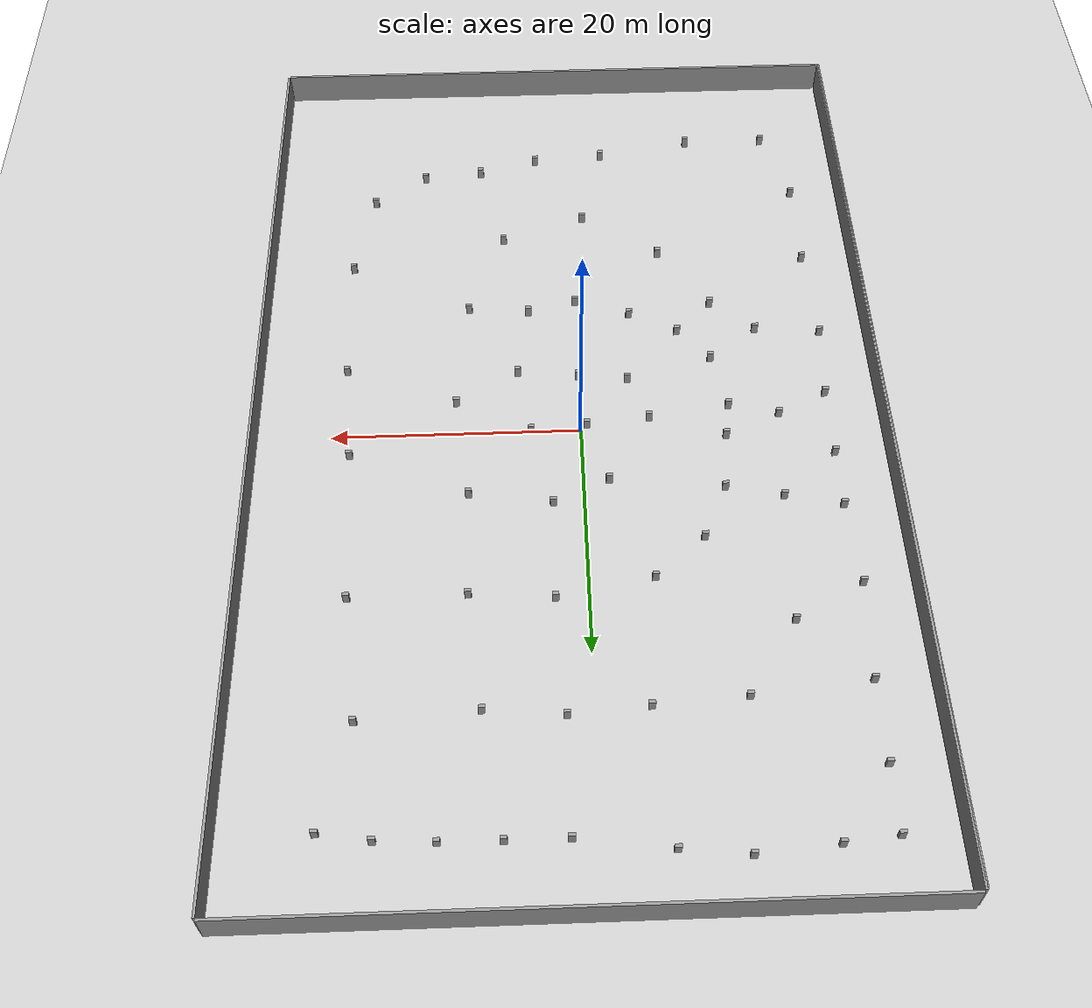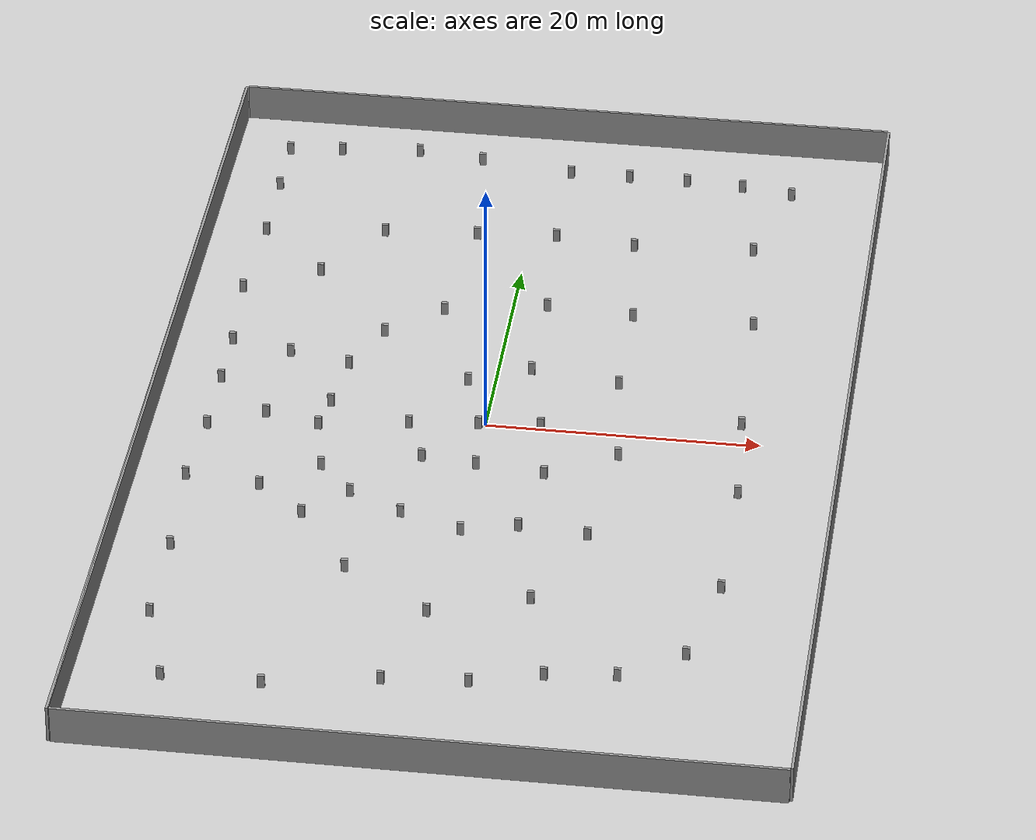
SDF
<sdf version="1.7">
 <world name="default">
  <light name="sun" type="directional">
   <pose>0 0 10 0 -0 0</pose>
   <diffuse>0.8 0.8 0.8 1</diffuse>
   <specular>0.2 0.2 0.2 1</specular>
   <attenuation>
    <range>1000</range>
    <constant>0.9</constant>
    <linear>0.01</linear>
    <quadratic>0.001</quadratic>
   </attenuation>
   <direction>-0.5 0.1 -0.9</direction>
   <spot><inner_angle>0</inner_angle><outer_angle>0</outer_angle><falloff>0</falloff></spot>
  </light>
  <model name="ground_plane">
   <static>1</static>
   <link name="link">
    <collision name="collision">
     <geometry><plane><normal>0 0 1</normal><size>100 100</size></plane></geometry>
     <surface>
      <contact><collide_bitmask>65535</collide_bitmask></contact>
      <friction><ode><mu>100</mu><mu2>50</mu2></ode></friction>
     </surface>
    </collision>
    <visual name="visual">
     <cast_shadows>0</cast_shadows>
     <geometry><plane><normal>0 0 1</normal><size>100 100</size></plane></geometry>
     <material>
      <script><uri>file://media/materials/scripts/gazebo.material</uri><name>Gazebo/Grey</name></script>
     </material>
    </visual>
   </link>
  </model>
  <gravity>0 0 -9.8</gravity>
  <magnetic_field>6e-06 2.3e-05 -4.2e-05</magnetic_field>
  <atmosphere type="adiabatic"/>
  <physics type="ode">
   <max_step_size>0.001</max_step_size>
   <real_time_factor>1</real_time_factor>
   <real_time_update_rate>1000</real_time_update_rate>
  </physics>
  <scene><ambient>0.4 0.4 0.4 1</ambient><background>0.7 0.7 0.7 1</background><shadows>1</shadows></scene>
  <spherical_coordinates>
   <surface_model>EARTH_WGS84</surface_model>
   <latitude_deg>0</latitude_deg>
   <longitude_deg>0</longitude_deg>
   <elevation>0</elevation>
   <heading_deg>0</heading_deg>
  </spherical_coordinates>
  <model name="grey_wall_four_closed">
   <link name="link">
    <pose>0.242491 26.6162 1.4 0 -0 0</pose>
    <inertial>
     <mass>1</mass>
     <inertia><ixx>1</ixx><ixy>0</ixy><ixz>0</ixz><iyy>1</iyy><iyz>0</iyz><izz>1</izz></inertia>
    </inertial>
    <visual name="visual">
     <cast_shadows>0</cast_shadows>
     <geometry><box><size>50 0.2 2.8</size></box></geometry>
     <material>
      <script>
       <uri>model://grey_wall/materials/scripts</uri>
       <uri>model://grey_wall/materials/textures</uri>
       <name>vrc/grey_wall</name>
      </script>
      <shader type="pixel"><normal_map>__default__</normal_map></shader>
      <ambient>1 1 1 1</ambient>
      <diffuse>1 1 1 1</diffuse>
      <specular>0 0 0 1</specular>
      <emissive>0 0 0 1</emissive>
     </material>
    </visual>
    <collision name="collision">
     <geometry><box><size>50 0.2 2.8</size></box></geometry>
     <surface>
      <friction>
       <ode><mu>1</mu><mu2>1</mu2><fdir1>0 0 0</fdir1><slip1>0</slip1><slip2>0</slip2></ode>
       <torsional>
        <coefficient>1</coefficient>
        <patch_radius>0</patch_radius>
        <surface_radius>0</surface_radius>
        <use_patch_radius>1</use_patch_radius>
        <ode><slip>0</slip></ode>
       </torsional>
      </friction>
      <bounce><restitution_coefficient>0</restitution_coefficient><threshold>1e+06</threshold></bounce>
      <contact>
       <collide_without_contact>0</collide_without_contact>
       <collide_without_contact_bitmask>1</collide_without_contact_bitmask>
       <collide_bitmask>1</collide_bitmask>
       <ode>
        <soft_cfm>0</soft_cfm>
        <soft_erp>0.2</soft_erp>
        <kp>1e+13</kp>
        <kd>1</kd>
        <max_vel>0.01</max_vel>
        <min_depth>0</min_depth>
       </ode>
       <bullet>
        <split_impulse>1</split_impulse>
        <split_impulse_penetration_threshold>-0.01</split_impulse_penetration_threshold>
        <soft_cfm>0</soft_cfm>
        <soft_erp>0.2</soft_erp>
        <kp>1e+13</kp>
        <kd>1</kd>
       </bullet>
      </contact>
     </surface>
    </collision>
   </link>
   <link name="link_clone">
    <pose>0.215468 -53.6091 1.4 0 -0 0</pose>
    <inertial>
     <mass>1</mass>
     <inertia><ixx>1</ixx><ixy>0</ixy><ixz>0</ixz><iyy>1</iyy><iyz>0</iyz><izz>1</izz></inertia>
    </inertial>
    <visual name="visual">
     <cast_shadows>0</cast_shadows>
     <geometry><box><size>50 0.2 2.8</size></box></geometry>
     <material>
      <script>
       <uri>model://grey_wall/materials/scripts</uri>
       <uri>model://grey_wall/materials/textures</uri>
       <name>vrc/grey_wall</name>
      </script>
      <shader type="pixel"><normal_map>__default__</normal_map></shader>
      <ambient>1 1 1 1</ambient>
      <diffuse>1 1 1 1</diffuse>
      <specular>0 0 0 1</specular>
      <emissive>0 0 0 1</emissive>
     </material>
    </visual>
    <collision name="collision">
     <geometry><box><size>50 0.2 2.8</size></box></geometry>
     <surface>
      <friction>
       <ode><mu>1</mu><mu2>1</mu2><fdir1>0 0 0</fdir1><slip1>0</slip1><slip2>0</slip2></ode>
       <torsional>
        <coefficient>1</coefficient>
        <patch_radius>0</patch_radius>
        <surface_radius>0</surface_radius>
        <use_patch_radius>1</use_patch_radius>
        <ode><slip>0</slip></ode>
       </torsional>
      </friction>
      <bounce><restitution_coefficient>0</restitution_coefficient><threshold>1e+06</threshold></bounce>
      <contact>
       <collide_without_contact>0</collide_without_contact>
       <collide_without_contact_bitmask>1</collide_without_contact_bitmask>
       <collide_bitmask>1</collide_bitmask>
       <ode>
        <soft_cfm>0</soft_cfm>
        <soft_erp>0.2</soft_erp>
        <kp>1e+13</kp>
        <kd>1</kd>
        <max_vel>0.01</max_vel>
        <min_depth>0</min_depth>
       </ode>
       <bullet>
        <split_impulse>1</split_impulse>
        <split_impulse_penetration_threshold>-0.01</split_impulse_penetration_threshold>
        <soft_cfm>0</soft_cfm>
        <soft_erp>0.2</soft_erp>
        <kp>1e+13</kp>
        <kd>1</kd>
       </bullet>
      </contact>
     </surface>
    </collision>
   </link>
   <link name="link_clone_0">
    <pose>25.3282 -13.5096 1.4 0 -0 0</pose>
    <inertial>
     <mass>1</mass>
     <inertia><ixx>1</ixx><ixy>0</ixy><ixz>0</ixz><iyy>1</iyy><iyz>0</iyz><izz>1</izz></inertia>
    </inertial>
    <visual name="visual">
     <cast_shadows>0</cast_shadows>
     <geometry><box><size>0.2 80 2.8</size></box></geometry>
     <material>
      <script>
       <uri>model://grey_wall/materials/scripts</uri>
       <uri>model://grey_wall/materials/textures</uri>
       <name>vrc/grey_wall</name>
      </script>
      <shader type="pixel"><normal_map>__default__</normal_map></shader>
      <ambient>1 1 1 1</ambient>
      <diffuse>1 1 1 1</diffuse>
      <specular>0 0 0 1</specular>
      <emissive>0 0 0 1</emissive>
     </material>
    </visual>
    <collision name="collision">
     <geometry><box><size>0.2 80 2.8</size></box></geometry>
     <surface>
      <friction>
       <ode><mu>1</mu><mu2>1</mu2><fdir1>0 0 0</fdir1><slip1>0</slip1><slip2>0</slip2></ode>
       <torsional>
        <coefficient>1</coefficient>
        <patch_radius>0</patch_radius>
        <surface_radius>0</surface_radius>
        <use_patch_radius>1</use_patch_radius>
        <ode><slip>0</slip></ode>
       </torsional>
      </friction>
      <bounce><restitution_coefficient>0</restitution_coefficient><threshold>1e+06</threshold></bounce>
      <contact>
       <collide_without_contact>0</collide_without_contact>
       <collide_without_contact_bitmask>1</collide_without_contact_bitmask>
       <collide_bitmask>1</collide_bitmask>
       <ode>
        <soft_cfm>0</soft_cfm>
        <soft_erp>0.2</soft_erp>
        <kp>1e+13</kp>
        <kd>1</kd>
        <max_vel>0.01</max_vel>
        <min_depth>0</min_depth>
       </ode>
       <bullet>
        <split_impulse>1</split_impulse>
        <split_impulse_penetration_threshold>-0.01</split_impulse_penetration_threshold>
        <soft_cfm>0</soft_cfm>
        <soft_erp>0.2</soft_erp>
        <kp>1e+13</kp>
        <kd>1</kd>
       </bullet>
      </contact>
     </surface>
    </collision>
   </link>
   <link name="link_clone_0_clone">
    <pose>-24.9038 -13.4873 1.4 0 -0 0</pose>
    <inertial>
     <mass>1</mass>
     <inertia><ixx>1</ixx><ixy>0</ixy><ixz>0</ixz><iyy>1</iyy><iyz>0</iyz><izz>1</izz></inertia>
    </inertial>
    <visual name="visual">
     <cast_shadows>0</cast_shadows>
     <geometry><box><size>0.2 80 2.8</size></box></geometry>
     <material>
      <script>
       <uri>model://grey_wall/materials/scripts</uri>
       <uri>model://grey_wall/materials/textures</uri>
       <name>vrc/grey_wall</name>
      </script>
      <shader type="pixel"><normal_map>__default__</normal_map></shader>
      <ambient>1 1 1 1</ambient>
      <diffuse>1 1 1 1</diffuse>
      <specular>0 0 0 1</specular>
      <emissive>0 0 0 1</emissive>
     </material>
    </visual>
    <collision name="collision">
     <geometry><box><size>0.2 80 2.8</size></box></geometry>
     <surface>
      <friction>
       <ode><mu>1</mu><mu2>1</mu2><fdir1>0 0 0</fdir1><slip1>0</slip1><slip2>0</slip2></ode>
       <torsional>
        <coefficient>1</coefficient>
        <patch_radius>0</patch_radius>
        <surface_radius>0</surface_radius>
        <use_patch_radius>1</use_patch_radius>
        <ode><slip>0</slip></ode>
       </torsional>
      </friction>
      <bounce><restitution_coefficient>0</restitution_coefficient><threshold>1e+06</threshold></bounce>
      <contact>
       <collide_without_contact>0</collide_without_contact>
       <collide_without_contact_bitmask>1</collide_without_contact_bitmask>
       <collide_bitmask>1</collide_bitmask>
       <ode>
        <soft_cfm>0</soft_cfm>
        <soft_erp>0.2</soft_erp>
        <kp>1e+13</kp>
        <kd>1</kd>
        <max_vel>0.01</max_vel>
        <min_depth>0</min_depth>
       </ode>
       <bullet>
        <split_impulse>1</split_impulse>
        <split_impulse_penetration_threshold>-0.01</split_impulse_penetration_threshold>
        <soft_cfm>0</soft_cfm>
        <soft_erp>0.2</soft_erp>
        <kp>1e+13</kp>
        <kd>1</kd>
       </bullet>
      </contact>
     </surface>
    </collision>
   </link>
   <link name="link_clone_0_clone_0">
    <pose>-24.9422 -13.6564 1.4 0 -0 0</pose>
    <inertial>
     <mass>1</mass>
     <inertia><ixx>1</ixx><ixy>0</ixy><ixz>0</ixz><iyy>1</iyy><iyz>0</iyz><izz>1</izz></inertia>
    </inertial>
    <visual name="visual">
     <cast_shadows>0</cast_shadows>
     <geometry><box><size>0.2 80 2.8</size></box></geometry>
     <material>
      <script>
       <uri>model://grey_wall/materials/scripts</uri>
       <uri>model://grey_wall/materials/textures</uri>
       <name>vrc/grey_wall</name>
      </script>
      <shader type="pixel"><normal_map>__default__</normal_map></shader>
      <ambient>1 1 1 1</ambient>
      <diffuse>1 1 1 1</diffuse>
      <specular>0 0 0 1</specular>
      <emissive>0 0 0 1</emissive>
     </material>
    </visual>
    <collision name="collision">
     <geometry><box><size>0.2 80 2.8</size></box></geometry>
     <surface>
      <friction>
       <ode><mu>1</mu><mu2>1</mu2><fdir1>0 0 0</fdir1><slip1>0</slip1><slip2>0</slip2></ode>
       <torsional>
        <coefficient>1</coefficient>
        <patch_radius>0</patch_radius>
        <surface_radius>0</surface_radius>
        <use_patch_radius>1</use_patch_radius>
        <ode><slip>0</slip></ode>
       </torsional>
      </friction>
      <bounce><restitution_coefficient>0</restitution_coefficient><threshold>1e+06</threshold></bounce>
      <contact>
       <collide_without_contact>0</collide_without_contact>
       <collide_without_contact_bitmask>1</collide_without_contact_bitmask>
       <collide_bitmask>1</collide_bitmask>
       <ode>
        <soft_cfm>0</soft_cfm>
        <soft_erp>0.2</soft_erp>
        <kp>1e+13</kp>
        <kd>1</kd>
        <max_vel>0.01</max_vel>
        <min_depth>0</min_depth>
       </ode>
       <bullet>
        <split_impulse>1</split_impulse>
        <split_impulse_penetration_threshold>-0.01</split_impulse_penetration_threshold>
        <soft_cfm>0</soft_cfm>
        <soft_erp>0.2</soft_erp>
        <kp>1e+13</kp>
        <kd>1</kd>
       </bullet>
      </contact>
     </surface>
    </collision>
   </link>
   <static>1</static>
   <pose>0.69016 12.8234 0 0 -0 0</pose>
  </model>
  <model name="box_race_car">
   <link name="link">
    <inertial>
     <mass>1</mass>
     <inertia>
      <ixx>0.166667</ixx>
      <ixy>0</ixy>
      <ixz>0</ixz>
      <iyy>0.166667</iyy>
      <iyz>0</iyz>
      <izz>0.166667</izz>
     </inertia>
    </inertial>
    <visual name="visual">
     <geometry><box><size>0.5 0.25 1</size></box></geometry>
     <material>
      <script><name>Gazebo/Grey</name><uri>file://media/materials/scripts/gazebo.material</uri></script>
      <shader type="pixel"><normal_map>__default__</normal_map></shader>
      <ambient>0.3 0.3 0.3 1</ambient>
      <diffuse>0.7 0.7 0.7 1</diffuse>
      <specular>0.01 0.01 0.01 1</specular>
      <emissive>0 0 0 1</emissive>
     </material>
    </visual>
    <collision name="collision">
     <geometry><box><size>0.5 0.25 1</size></box></geometry>
     <surface>
      <friction>
       <ode><mu>1</mu><mu2>1</mu2><fdir1>0 0 0</fdir1><slip1>0</slip1><slip2>0</slip2></ode>
       <torsional>
        <coefficient>1</coefficient>
        <patch_radius>0</patch_radius>
        <surface_radius>0</surface_radius>
        <use_patch_radius>1</use_patch_radius>
        <ode><slip>0</slip></ode>
       </torsional>
      </friction>
      <bounce><restitution_coefficient>0</restitution_coefficient><threshold>1e+06</threshold></bounce>
      <contact>
       <collide_without_contact>0</collide_without_contact>
       <collide_without_contact_bitmask>1</collide_without_contact_bitmask>
       <collide_bitmask>1</collide_bitmask>
       <ode>
        <soft_cfm>0</soft_cfm>
        <soft_erp>0.2</soft_erp>
        <kp>1e+13</kp>
        <kd>1</kd>
        <max_vel>0.01</max_vel>
        <min_depth>0</min_depth>
       </ode>
       <bullet>
        <split_impulse>1</split_impulse>
        <split_impulse_penetration_threshold>-0.01</split_impulse_penetration_threshold>
        <soft_cfm>0</soft_cfm>
        <soft_erp>0.2</soft_erp>
        <kp>1e+13</kp>
        <kd>1</kd>
       </bullet>
      </contact>
     </surface>
    </collision>
   </link>
   <static>0</static>
   <pose>19.1479 33.1062 0.499999 -2e-06 4e-06 4.6e-05</pose>
  </model>
  <model name="box_race_car_clone">
   <link name="link">
    <inertial>
     <mass>1</mass>
     <inertia>
      <ixx>0.166667</ixx>
      <ixy>0</ixy>
      <ixz>0</ixz>
      <iyy>0.166667</iyy>
      <iyz>0</iyz>
      <izz>0.166667</izz>
     </inertia>
    </inertial>
    <visual name="visual">
     <geometry><box><size>0.5 0.25 1</size></box></geometry>
     <material>
      <script><name>Gazebo/Grey</name><uri>file://media/materials/scripts/gazebo.material</uri></script>
      <shader type="pixel"><normal_map>__default__</normal_map></shader>
      <ambient>0.3 0.3 0.3 1</ambient>
      <diffuse>0.7 0.7 0.7 1</diffuse>
      <specular>0.01 0.01 0.01 1</specular>
      <emissive>0 0 0 1</emissive>
     </material>
    </visual>
    <collision name="collision">
     <geometry><box><size>0.5 0.25 1</size></box></geometry>
     <surface>
      <friction>
       <ode><mu>1</mu><mu2>1</mu2><fdir1>0 0 0</fdir1><slip1>0</slip1><slip2>0</slip2></ode>
       <torsional>
        <coefficient>1</coefficient>
        <patch_radius>0</patch_radius>
        <surface_radius>0</surface_radius>
        <use_patch_radius>1</use_patch_radius>
        <ode><slip>0</slip></ode>
       </torsional>
      </friction>
      <bounce><restitution_coefficient>0</restitution_coefficient><threshold>1e+06</threshold></bounce>
      <contact>
       <collide_without_contact>0</collide_without_contact>
       <collide_without_contact_bitmask>1</collide_without_contact_bitmask>
       <collide_bitmask>1</collide_bitmask>
       <ode>
        <soft_cfm>0</soft_cfm>
        <soft_erp>0.2</soft_erp>
        <kp>1e+13</kp>
        <kd>1</kd>
        <max_vel>0.01</max_vel>
        <min_depth>0</min_depth>
       </ode>
       <bullet>
        <split_impulse>1</split_impulse>
        <split_impulse_penetration_threshold>-0.01</split_impulse_penetration_threshold>
        <soft_cfm>0</soft_cfm>
        <soft_erp>0.2</soft_erp>
        <kp>1e+13</kp>
        <kd>1</kd>
       </bullet>
      </contact>
     </surface>
    </collision>
   </link>
   <static>0</static>
   <pose>15.3102 33.7458 0.499999 -3e-06 -4e-06 0.000186</pose>
  </model>
  <model name="box_race_car_clone_0">
   <link name="link">
    <inertial>
     <mass>1</mass>
     <inertia>
      <ixx>0.166667</ixx>
      <ixy>0</ixy>
      <ixz>0</ixz>
      <iyy>0.166667</iyy>
      <iyz>0</iyz>
      <izz>0.166667</izz>
     </inertia>
    </inertial>
    <visual name="visual">
     <geometry><box><size>0.5 0.25 1</size></box></geometry>
     <material>
      <script><name>Gazebo/Grey</name><uri>file://media/materials/scripts/gazebo.material</uri></script>
      <shader type="pixel"><normal_map>__default__</normal_map></shader>
      <ambient>0.3 0.3 0.3 1</ambient>
      <diffuse>0.7 0.7 0.7 1</diffuse>
      <specular>0.01 0.01 0.01 1</specular>
      <emissive>0 0 0 1</emissive>
     </material>
    </visual>
    <collision name="collision">
     <geometry><box><size>0.5 0.25 1</size></box></geometry>
     <surface>
      <friction>
       <ode><mu>1</mu><mu2>1</mu2><fdir1>0 0 0</fdir1><slip1>0</slip1><slip2>0</slip2></ode>
       <torsional>
        <coefficient>1</coefficient>
        <patch_radius>0</patch_radius>
        <surface_radius>0</surface_radius>
        <use_patch_radius>1</use_patch_radius>
        <ode><slip>0</slip></ode>
       </torsional>
      </friction>
      <bounce><restitution_coefficient>0</restitution_coefficient><threshold>1e+06</threshold></bounce>
      <contact>
       <collide_without_contact>0</collide_without_contact>
       <collide_without_contact_bitmask>1</collide_without_contact_bitmask>
       <collide_bitmask>1</collide_bitmask>
       <ode>
        <soft_cfm>0</soft_cfm>
        <soft_erp>0.2</soft_erp>
        <kp>1e+13</kp>
        <kd>1</kd>
        <max_vel>0.01</max_vel>
        <min_depth>0</min_depth>
       </ode>
       <bullet>
        <split_impulse>1</split_impulse>
        <split_impulse_penetration_threshold>-0.01</split_impulse_penetration_threshold>
        <soft_cfm>0</soft_cfm>
        <soft_erp>0.2</soft_erp>
        <kp>1e+13</kp>
        <kd>1</kd>
       </bullet>
      </contact>
     </surface>
    </collision>
   </link>
   <static>0</static>
   <pose>11 34 0.500001 -0 -2e-06 2e-06</pose>
  </model>
  <model name="box_race_car_clone_1">
   <link name="link">
    <inertial>
     <mass>1</mass>
     <inertia>
      <ixx>0.166667</ixx>
      <ixy>0</ixy>
      <ixz>0</ixz>
      <iyy>0.166667</iyy>
      <iyz>0</iyz>
      <izz>0.166667</izz>
     </inertia>
    </inertial>
    <visual name="visual">
     <geometry><box><size>0.5 0.25 1</size></box></geometry>
     <material>
      <script><name>Gazebo/Grey</name><uri>file://media/materials/scripts/gazebo.material</uri></script>
      <shader type="pixel"><normal_map>__default__</normal_map></shader>
      <ambient>0.3 0.3 0.3 1</ambient>
      <diffuse>0.7 0.7 0.7 1</diffuse>
      <specular>0.01 0.01 0.01 1</specular>
      <emissive>0 0 0 1</emissive>
     </material>
    </visual>
    <collision name="collision">
     <geometry><box><size>0.5 0.25 1</size></box></geometry>
     <surface>
      <friction>
       <ode><mu>1</mu><mu2>1</mu2><fdir1>0 0 0</fdir1><slip1>0</slip1><slip2>0</slip2></ode>
       <torsional>
        <coefficient>1</coefficient>
        <patch_radius>0</patch_radius>
        <surface_radius>0</surface_radius>
        <use_patch_radius>1</use_patch_radius>
        <ode><slip>0</slip></ode>
       </torsional>
      </friction>
      <bounce><restitution_coefficient>0</restitution_coefficient><threshold>1e+06</threshold></bounce>
      <contact>
       <collide_without_contact>0</collide_without_contact>
       <collide_without_contact_bitmask>1</collide_without_contact_bitmask>
       <collide_bitmask>1</collide_bitmask>
       <ode>
        <soft_cfm>0</soft_cfm>
        <soft_erp>0.2</soft_erp>
        <kp>1e+13</kp>
        <kd>1</kd>
        <max_vel>0.01</max_vel>
        <min_depth>0</min_depth>
       </ode>
       <bullet>
        <split_impulse>1</split_impulse>
        <split_impulse_penetration_threshold>-0.01</split_impulse_penetration_threshold>
        <soft_cfm>0</soft_cfm>
        <soft_erp>0.2</soft_erp>
        <kp>1e+13</kp>
        <kd>1</kd>
       </bullet>
      </contact>
     </surface>
    </collision>
   </link>
   <static>0</static>
   <pose>6.53822 34 0.500001 -0 -2e-06 0.000223</pose>
  </model>
  <model name="box_race_car_clone_2">
   <link name="link">
    <inertial>
     <mass>1</mass>
     <inertia>
      <ixx>0.166667</ixx>
      <ixy>0</ixy>
      <ixz>0</ixz>
      <iyy>0.166667</iyy>
      <iyz>0</iyz>
      <izz>0.166667</izz>
     </inertia>
    </inertial>
    <visual name="visual">
     <geometry><box><size>0.5 0.25 1</size></box></geometry>
     <material>
      <script><name>Gazebo/Grey</name><uri>file://media/materials/scripts/gazebo.material</uri></script>
      <shader type="pixel"><normal_map>__default__</normal_map></shader>
      <ambient>0.3 0.3 0.3 1</ambient>
      <diffuse>0.7 0.7 0.7 1</diffuse>
      <specular>0.01 0.01 0.01 1</specular>
      <emissive>0 0 0 1</emissive>
     </material>
    </visual>
    <collision name="collision">
     <geometry><box><size>0.5 0.25 1</size></box></geometry>
     <surface>
      <friction>
       <ode><mu>1</mu><mu2>1</mu2><fdir1>0 0 0</fdir1><slip1>0</slip1><slip2>0</slip2></ode>
       <torsional>
        <coefficient>1</coefficient>
        <patch_radius>0</patch_radius>
        <surface_radius>0</surface_radius>
        <use_patch_radius>1</use_patch_radius>
        <ode><slip>0</slip></ode>
       </torsional>
      </friction>
      <bounce><restitution_coefficient>0</restitution_coefficient><threshold>1e+06</threshold></bounce>
      <contact>
       <collide_without_contact>0</collide_without_contact>
       <collide_without_contact_bitmask>1</collide_without_contact_bitmask>
       <collide_bitmask>1</collide_bitmask>
       <ode>
        <soft_cfm>0</soft_cfm>
        <soft_erp>0.2</soft_erp>
        <kp>1e+13</kp>
        <kd>1</kd>
        <max_vel>0.01</max_vel>
        <min_depth>0</min_depth>
       </ode>
       <bullet>
        <split_impulse>1</split_impulse>
        <split_impulse_penetration_threshold>-0.01</split_impulse_penetration_threshold>
        <soft_cfm>0</soft_cfm>
        <soft_erp>0.2</soft_erp>
        <kp>1e+13</kp>
        <kd>1</kd>
       </bullet>
      </contact>
     </surface>
    </collision>
   </link>
   <static>0</static>
   <pose>1.99999 34 0.499999 2e-06 -4e-06 -3.5e-05</pose>
  </model>
  <model name="box_race_car_clone_3">
   <link name="link">
    <inertial>
     <mass>1</mass>
     <inertia>
      <ixx>0.166667</ixx>
      <ixy>0</ixy>
      <ixz>0</ixz>
      <iyy>0.166667</iyy>
      <iyz>0</iyz>
      <izz>0.166667</izz>
     </inertia>
    </inertial>
    <visual name="visual">
     <geometry><box><size>0.5 0.25 1</size></box></geometry>
     <material>
      <script><name>Gazebo/Grey</name><uri>file://media/materials/scripts/gazebo.material</uri></script>
      <shader type="pixel"><normal_map>__default__</normal_map></shader>
      <ambient>0.3 0.3 0.3 1</ambient>
      <diffuse>0.7 0.7 0.7 1</diffuse>
      <specular>0.01 0.01 0.01 1</specular>
      <emissive>0 0 0 1</emissive>
     </material>
    </visual>
    <collision name="collision">
     <geometry><box><size>0.5 0.25 1</size></box></geometry>
     <surface>
      <friction>
       <ode><mu>1</mu><mu2>1</mu2><fdir1>0 0 0</fdir1><slip1>0</slip1><slip2>0</slip2></ode>
       <torsional>
        <coefficient>1</coefficient>
        <patch_radius>0</patch_radius>
        <surface_radius>0</surface_radius>
        <use_patch_radius>1</use_patch_radius>
        <ode><slip>0</slip></ode>
       </torsional>
      </friction>
      <bounce><restitution_coefficient>0</restitution_coefficient><threshold>1e+06</threshold></bounce>
      <contact>
       <collide_without_contact>0</collide_without_contact>
       <collide_without_contact_bitmask>1</collide_without_contact_bitmask>
       <collide_bitmask>1</collide_bitmask>
       <ode>
        <soft_cfm>0</soft_cfm>
        <soft_erp>0.2</soft_erp>
        <kp>1e+13</kp>
        <kd>1</kd>
        <max_vel>0.01</max_vel>
        <min_depth>0</min_depth>
       </ode>
       <bullet>
        <split_impulse>1</split_impulse>
        <split_impulse_penetration_threshold>-0.01</split_impulse_penetration_threshold>
        <soft_cfm>0</soft_cfm>
        <soft_erp>0.2</soft_erp>
        <kp>1e+13</kp>
        <kd>1</kd>
       </bullet>
      </contact>
     </surface>
    </collision>
   </link>
   <static>0</static>
   <pose>-5 35 0.499999 -2e-06 -4e-06 3.4e-05</pose>
  </model>
  <model name="box_race_car_clone_4">
   <link name="link">
    <inertial>
     <mass>1</mass>
     <inertia>
      <ixx>0.166667</ixx>
      <ixy>0</ixy>
      <ixz>0</ixz>
      <iyy>0.166667</iyy>
      <iyz>0</iyz>
      <izz>0.166667</izz>
     </inertia>
    </inertial>
    <visual name="visual">
     <geometry><box><size>0.5 0.25 1</size></box></geometry>
     <material>
      <script><name>Gazebo/Grey</name><uri>file://media/materials/scripts/gazebo.material</uri></script>
      <shader type="pixel"><normal_map>__default__</normal_map></shader>
      <ambient>0.3 0.3 0.3 1</ambient>
      <diffuse>0.7 0.7 0.7 1</diffuse>
      <specular>0.01 0.01 0.01 1</specular>
      <emissive>0 0 0 1</emissive>
     </material>
    </visual>
    <collision name="collision">
     <geometry><box><size>0.5 0.25 1</size></box></geometry>
     <surface>
      <friction>
       <ode><mu>1</mu><mu2>1</mu2><fdir1>0 0 0</fdir1><slip1>0</slip1><slip2>0</slip2></ode>
       <torsional>
        <coefficient>1</coefficient>
        <patch_radius>0</patch_radius>
        <surface_radius>0</surface_radius>
        <use_patch_radius>1</use_patch_radius>
        <ode><slip>0</slip></ode>
       </torsional>
      </friction>
      <bounce><restitution_coefficient>0</restitution_coefficient><threshold>1e+06</threshold></bounce>
      <contact>
       <collide_without_contact>0</collide_without_contact>
       <collide_without_contact_bitmask>1</collide_without_contact_bitmask>
       <collide_bitmask>1</collide_bitmask>
       <ode>
        <soft_cfm>0</soft_cfm>
        <soft_erp>0.2</soft_erp>
        <kp>1e+13</kp>
        <kd>1</kd>
        <max_vel>0.01</max_vel>
        <min_depth>0</min_depth>
       </ode>
       <bullet>
        <split_impulse>1</split_impulse>
        <split_impulse_penetration_threshold>-0.01</split_impulse_penetration_threshold>
        <soft_cfm>0</soft_cfm>
        <soft_erp>0.2</soft_erp>
        <kp>1e+13</kp>
        <kd>1</kd>
       </bullet>
      </contact>
     </surface>
    </collision>
   </link>
   <static>0</static>
   <pose>-10 35.5754 0.499999 -3e-06 -4e-06 -0.000403</pose>
  </model>
  <model name="box_race_car_clone_5">
   <link name="link">
    <inertial>
     <mass>1</mass>
     <inertia>
      <ixx>0.166667</ixx>
      <ixy>0</ixy>
      <ixz>0</ixz>
      <iyy>0.166667</iyy>
      <iyz>0</iyz>
      <izz>0.166667</izz>
     </inertia>
    </inertial>
    <visual name="visual">
     <geometry><box><size>0.5 0.25 1</size></box></geometry>
     <material>
      <script><name>Gazebo/Grey</name><uri>file://media/materials/scripts/gazebo.material</uri></script>
      <shader type="pixel"><normal_map>__default__</normal_map></shader>
      <ambient>0.3 0.3 0.3 1</ambient>
      <diffuse>0.7 0.7 0.7 1</diffuse>
      <specular>0.01 0.01 0.01 1</specular>
      <emissive>0 0 0 1</emissive>
     </material>
    </visual>
    <collision name="collision">
     <geometry><box><size>0.5 0.25 1</size></box></geometry>
     <surface>
      <friction>
       <ode><mu>1</mu><mu2>1</mu2><fdir1>0 0 0</fdir1><slip1>0</slip1><slip2>0</slip2></ode>
       <torsional>
        <coefficient>1</coefficient>
        <patch_radius>0</patch_radius>
        <surface_radius>0</surface_radius>
        <use_patch_radius>1</use_patch_radius>
        <ode><slip>0</slip></ode>
       </torsional>
      </friction>
      <bounce><restitution_coefficient>0</restitution_coefficient><threshold>1e+06</threshold></bounce>
      <contact>
       <collide_without_contact>0</collide_without_contact>
       <collide_without_contact_bitmask>1</collide_without_contact_bitmask>
       <collide_bitmask>1</collide_bitmask>
       <ode>
        <soft_cfm>0</soft_cfm>
        <soft_erp>0.2</soft_erp>
        <kp>1e+13</kp>
        <kd>1</kd>
        <max_vel>0.01</max_vel>
        <min_depth>0</min_depth>
       </ode>
       <bullet>
        <split_impulse>1</split_impulse>
        <split_impulse_penetration_threshold>-0.01</split_impulse_penetration_threshold>
        <soft_cfm>0</soft_cfm>
        <soft_erp>0.2</soft_erp>
        <kp>1e+13</kp>
        <kd>1</kd>
       </bullet>
      </contact>
     </surface>
    </collision>
   </link>
   <static>0</static>
   <pose>-16 35 0.499999 -1e-06 4e-06 -0.000117</pose>
  </model>
  <model name="box_race_car_clone_6">
   <link name="link">
    <inertial>
     <mass>1</mass>
     <inertia>
      <ixx>0.166667</ixx>
      <ixy>0</ixy>
      <ixz>0</ixz>
      <iyy>0.166667</iyy>
      <iyz>0</iyz>
      <izz>0.166667</izz>
     </inertia>
    </inertial>
    <visual name="visual">
     <geometry><box><size>0.5 0.25 1</size></box></geometry>
     <material>
      <script><name>Gazebo/Grey</name><uri>file://media/materials/scripts/gazebo.material</uri></script>
      <shader type="pixel"><normal_map>__default__</normal_map></shader>
      <ambient>0.3 0.3 0.3 1</ambient>
      <diffuse>0.7 0.7 0.7 1</diffuse>
      <specular>0.01 0.01 0.01 1</specular>
      <emissive>0 0 0 1</emissive>
     </material>
    </visual>
    <collision name="collision">
     <geometry><box><size>0.5 0.25 1</size></box></geometry>
     <surface>
      <friction>
       <ode><mu>1</mu><mu2>1</mu2><fdir1>0 0 0</fdir1><slip1>0</slip1><slip2>0</slip2></ode>
       <torsional>
        <coefficient>1</coefficient>
        <patch_radius>0</patch_radius>
        <surface_radius>0</surface_radius>
        <use_patch_radius>1</use_patch_radius>
        <ode><slip>0</slip></ode>
       </torsional>
      </friction>
      <bounce><restitution_coefficient>0</restitution_coefficient><threshold>1e+06</threshold></bounce>
      <contact>
       <collide_without_contact>0</collide_without_contact>
       <collide_without_contact_bitmask>1</collide_without_contact_bitmask>
       <collide_bitmask>1</collide_bitmask>
       <ode>
        <soft_cfm>0</soft_cfm>
        <soft_erp>0.2</soft_erp>
        <kp>1e+13</kp>
        <kd>1</kd>
        <max_vel>0.01</max_vel>
        <min_depth>0</min_depth>
       </ode>
       <bullet>
        <split_impulse>1</split_impulse>
        <split_impulse_penetration_threshold>-0.01</split_impulse_penetration_threshold>
        <soft_cfm>0</soft_cfm>
        <soft_erp>0.2</soft_erp>
        <kp>1e+13</kp>
        <kd>1</kd>
       </bullet>
      </contact>
     </surface>
    </collision>
   </link>
   <static>0</static>
   <pose>-20 34.5713 0.500001 1e-06 -2e-06 7e-05</pose>
  </model>
  <model name="box_race_car_clone_7">
   <link name="link">
    <inertial>
     <mass>1</mass>
     <inertia>
      <ixx>0.166667</ixx>
      <ixy>0</ixy>
      <ixz>0</ixz>
      <iyy>0.166667</iyy>
      <iyz>0</iyz>
      <izz>0.166667</izz>
     </inertia>
    </inertial>
    <visual name="visual">
     <geometry><box><size>0.5 0.25 1</size></box></geometry>
     <material>
      <script><name>Gazebo/Grey</name><uri>file://media/materials/scripts/gazebo.material</uri></script>
      <shader type="pixel"><normal_map>__default__</normal_map></shader>
      <ambient>0.3 0.3 0.3 1</ambient>
      <diffuse>0.7 0.7 0.7 1</diffuse>
      <specular>0.01 0.01 0.01 1</specular>
      <emissive>0 0 0 1</emissive>
     </material>
    </visual>
    <collision name="collision">
     <geometry><box><size>0.5 0.25 1</size></box></geometry>
     <surface>
      <friction>
       <ode><mu>1</mu><mu2>1</mu2><fdir1>0 0 0</fdir1><slip1>0</slip1><slip2>0</slip2></ode>
       <torsional>
        <coefficient>1</coefficient>
        <patch_radius>0</patch_radius>
        <surface_radius>0</surface_radius>
        <use_patch_radius>1</use_patch_radius>
        <ode><slip>0</slip></ode>
       </torsional>
      </friction>
      <bounce><restitution_coefficient>0</restitution_coefficient><threshold>1e+06</threshold></bounce>
      <contact>
       <collide_without_contact>0</collide_without_contact>
       <collide_without_contact_bitmask>1</collide_without_contact_bitmask>
       <collide_bitmask>1</collide_bitmask>
       <ode>
        <soft_cfm>0</soft_cfm>
        <soft_erp>0.2</soft_erp>
        <kp>1e+13</kp>
        <kd>1</kd>
        <max_vel>0.01</max_vel>
        <min_depth>0</min_depth>
       </ode>
       <bullet>
        <split_impulse>1</split_impulse>
        <split_impulse_penetration_threshold>-0.01</split_impulse_penetration_threshold>
        <soft_cfm>0</soft_cfm>
        <soft_erp>0.2</soft_erp>
        <kp>1e+13</kp>
        <kd>1</kd>
       </bullet>
      </contact>
     </surface>
    </collision>
   </link>
   <static>0</static>
   <pose>-20 29.4541 0.499999 -1e-06 4e-06 0.000303</pose>
  </model>
  <model name="box_race_car_clone_8">
   <link name="link">
    <inertial>
     <mass>1</mass>
     <inertia>
      <ixx>0.166667</ixx>
      <ixy>0</ixy>
      <ixz>0</ixz>
      <iyy>0.166667</iyy>
      <iyz>0</iyz>
      <izz>0.166667</izz>
     </inertia>
    </inertial>
    <visual name="visual">
     <geometry><box><size>0.5 0.25 1</size></box></geometry>
     <material>
      <script><name>Gazebo/Grey</name><uri>file://media/materials/scripts/gazebo.material</uri></script>
      <shader type="pixel"><normal_map>__default__</normal_map></shader>
      <ambient>0.3 0.3 0.3 1</ambient>
      <diffuse>0.7 0.7 0.7 1</diffuse>
      <specular>0.01 0.01 0.01 1</specular>
      <emissive>0 0 0 1</emissive>
     </material>
    </visual>
    <collision name="collision">
     <geometry><box><size>0.5 0.25 1</size></box></geometry>
     <surface>
      <friction>
       <ode><mu>1</mu><mu2>1</mu2><fdir1>0 0 0</fdir1><slip1>0</slip1><slip2>0</slip2></ode>
       <torsional>
        <coefficient>1</coefficient>
        <patch_radius>0</patch_radius>
        <surface_radius>0</surface_radius>
        <use_patch_radius>1</use_patch_radius>
        <ode><slip>0</slip></ode>
       </torsional>
      </friction>
      <bounce><restitution_coefficient>0</restitution_coefficient><threshold>1e+06</threshold></bounce>
      <contact>
       <collide_without_contact>0</collide_without_contact>
       <collide_without_contact_bitmask>1</collide_without_contact_bitmask>
       <collide_bitmask>1</collide_bitmask>
       <ode>
        <soft_cfm>0</soft_cfm>
        <soft_erp>0.2</soft_erp>
        <kp>1e+13</kp>
        <kd>1</kd>
        <max_vel>0.01</max_vel>
        <min_depth>0</min_depth>
       </ode>
       <bullet>
        <split_impulse>1</split_impulse>
        <split_impulse_penetration_threshold>-0.01</split_impulse_penetration_threshold>
        <soft_cfm>0</soft_cfm>
        <soft_erp>0.2</soft_erp>
        <kp>1e+13</kp>
        <kd>1</kd>
       </bullet>
      </contact>
     </surface>
    </collision>
   </link>
   <static>0</static>
   <pose>-20 23 0.500001 0 -2e-06 -0.000185</pose>
  </model>
  <model name="box_race_car_clone_9">
   <link name="link">
    <inertial>
     <mass>1</mass>
     <inertia>
      <ixx>0.166667</ixx>
      <ixy>0</ixy>
      <ixz>0</ixz>
      <iyy>0.166667</iyy>
      <iyz>0</iyz>
      <izz>0.166667</izz>
     </inertia>
    </inertial>
    <visual name="visual">
     <geometry><box><size>0.5 0.25 1</size></box></geometry>
     <material>
      <script><name>Gazebo/Grey</name><uri>file://media/materials/scripts/gazebo.material</uri></script>
      <shader type="pixel"><normal_map>__default__</normal_map></shader>
      <ambient>0.3 0.3 0.3 1</ambient>
      <diffuse>0.7 0.7 0.7 1</diffuse>
      <specular>0.01 0.01 0.01 1</specular>
      <emissive>0 0 0 1</emissive>
     </material>
    </visual>
    <collision name="collision">
     <geometry><box><size>0.5 0.25 1</size></box></geometry>
     <surface>
      <friction>
       <ode><mu>1</mu><mu2>1</mu2><fdir1>0 0 0</fdir1><slip1>0</slip1><slip2>0</slip2></ode>
       <torsional>
        <coefficient>1</coefficient>
        <patch_radius>0</patch_radius>
        <surface_radius>0</surface_radius>
        <use_patch_radius>1</use_patch_radius>
        <ode><slip>0</slip></ode>
       </torsional>
      </friction>
      <bounce><restitution_coefficient>0</restitution_coefficient><threshold>1e+06</threshold></bounce>
      <contact>
       <collide_without_contact>0</collide_without_contact>
       <collide_without_contact_bitmask>1</collide_without_contact_bitmask>
       <collide_bitmask>1</collide_bitmask>
       <ode>
        <soft_cfm>0</soft_cfm>
        <soft_erp>0.2</soft_erp>
        <kp>1e+13</kp>
        <kd>1</kd>
        <max_vel>0.01</max_vel>
        <min_depth>0</min_depth>
       </ode>
       <bullet>
        <split_impulse>1</split_impulse>
        <split_impulse_penetration_threshold>-0.01</split_impulse_penetration_threshold>
        <soft_cfm>0</soft_cfm>
        <soft_erp>0.2</soft_erp>
        <kp>1e+13</kp>
        <kd>1</kd>
       </bullet>
      </contact>
     </surface>
    </collision>
   </link>
   <static>0</static>
   <pose>-20.4173 15 0.499999 -3e-06 -4e-06 0.000468</pose>
  </model>
  <model name="box_race_car_clone_10">
   <link name="link">
    <inertial>
     <mass>1</mass>
     <inertia>
      <ixx>0.166667</ixx>
      <ixy>0</ixy>
      <ixz>0</ixz>
      <iyy>0.166667</iyy>
      <iyz>0</iyz>
      <izz>0.166667</izz>
     </inertia>
    </inertial>
    <visual name="visual">
     <geometry><box><size>0.5 0.25 1</size></box></geometry>
     <material>
      <script><name>Gazebo/Grey</name><uri>file://media/materials/scripts/gazebo.material</uri></script>
      <shader type="pixel"><normal_map>__default__</normal_map></shader>
      <ambient>0.3 0.3 0.3 1</ambient>
      <diffuse>0.7 0.7 0.7 1</diffuse>
      <specular>0.01 0.01 0.01 1</specular>
      <emissive>0 0 0 1</emissive>
     </material>
    </visual>
    <collision name="collision">
     <geometry><box><size>0.5 0.25 1</size></box></geometry>
     <surface>
      <friction>
       <ode><mu>1</mu><mu2>1</mu2><fdir1>0 0 0</fdir1><slip1>0</slip1><slip2>0</slip2></ode>
       <torsional>
        <coefficient>1</coefficient>
        <patch_radius>0</patch_radius>
        <surface_radius>0</surface_radius>
        <use_patch_radius>1</use_patch_radius>
        <ode><slip>0</slip></ode>
       </torsional>
      </friction>
      <bounce><restitution_coefficient>0</restitution_coefficient><threshold>1e+06</threshold></bounce>
      <contact>
       <collide_without_contact>0</collide_without_contact>
       <collide_without_contact_bitmask>1</collide_without_contact_bitmask>
       <collide_bitmask>1</collide_bitmask>
       <ode>
        <soft_cfm>0</soft_cfm>
        <soft_erp>0.2</soft_erp>
        <kp>1e+13</kp>
        <kd>1</kd>
        <max_vel>0.01</max_vel>
        <min_depth>0</min_depth>
       </ode>
       <bullet>
        <split_impulse>1</split_impulse>
        <split_impulse_penetration_threshold>-0.01</split_impulse_penetration_threshold>
        <soft_cfm>0</soft_cfm>
        <soft_erp>0.2</soft_erp>
        <kp>1e+13</kp>
        <kd>1</kd>
       </bullet>
      </contact>
     </surface>
    </collision>
   </link>
   <static>0</static>
   <pose>-20 8 0.499999 1e-06 4e-06 0.000228</pose>
  </model>
  <model name="box_race_car_clone_11">
   <link name="link">
    <inertial>
     <mass>1</mass>
     <inertia>
      <ixx>0.166667</ixx>
      <ixy>0</ixy>
      <ixz>0</ixz>
      <iyy>0.166667</iyy>
      <iyz>0</iyz>
      <izz>0.166667</izz>
     </inertia>
    </inertial>
    <visual name="visual">
     <geometry><box><size>0.5 0.25 1</size></box></geometry>
     <material>
      <script><name>Gazebo/Grey</name><uri>file://media/materials/scripts/gazebo.material</uri></script>
      <shader type="pixel"><normal_map>__default__</normal_map></shader>
      <ambient>0.3 0.3 0.3 1</ambient>
      <diffuse>0.7 0.7 0.7 1</diffuse>
      <specular>0.01 0.01 0.01 1</specular>
      <emissive>0 0 0 1</emissive>
     </material>
    </visual>
    <collision name="collision">
     <geometry><box><size>0.5 0.25 1</size></box></geometry>
     <surface>
      <friction>
       <ode><mu>1</mu><mu2>1</mu2><fdir1>0 0 0</fdir1><slip1>0</slip1><slip2>0</slip2></ode>
       <torsional>
        <coefficient>1</coefficient>
        <patch_radius>0</patch_radius>
        <surface_radius>0</surface_radius>
        <use_patch_radius>1</use_patch_radius>
        <ode><slip>0</slip></ode>
       </torsional>
      </friction>
      <bounce><restitution_coefficient>0</restitution_coefficient><threshold>1e+06</threshold></bounce>
      <contact>
       <collide_without_contact>0</collide_without_contact>
       <collide_without_contact_bitmask>1</collide_without_contact_bitmask>
       <collide_bitmask>1</collide_bitmask>
       <ode>
        <soft_cfm>0</soft_cfm>
        <soft_erp>0.2</soft_erp>
        <kp>1e+13</kp>
        <kd>1</kd>
        <max_vel>0.01</max_vel>
        <min_depth>0</min_depth>
       </ode>
       <bullet>
        <split_impulse>1</split_impulse>
        <split_impulse_penetration_threshold>-0.01</split_impulse_penetration_threshold>
        <soft_cfm>0</soft_cfm>
        <soft_erp>0.2</soft_erp>
        <kp>1e+13</kp>
        <kd>1</kd>
       </bullet>
      </contact>
     </surface>
    </collision>
   </link>
   <static>0</static>
   <pose>-20 3 0.500001 1e-06 -2e-06 0.000143</pose>
  </model>
  <model name="box_race_car_clone_12">
   <link name="link">
    <inertial>
     <mass>1</mass>
     <inertia>
      <ixx>0.166667</ixx>
      <ixy>0</ixy>
      <ixz>0</ixz>
      <iyy>0.166667</iyy>
      <iyz>0</iyz>
      <izz>0.166667</izz>
     </inertia>
    </inertial>
    <visual name="visual">
     <geometry><box><size>0.5 0.25 1</size></box></geometry>
     <material>
      <script><name>Gazebo/Grey</name><uri>file://media/materials/scripts/gazebo.material</uri></script>
      <shader type="pixel"><normal_map>__default__</normal_map></shader>
      <ambient>0.3 0.3 0.3 1</ambient>
      <diffuse>0.7 0.7 0.7 1</diffuse>
      <specular>0.01 0.01 0.01 1</specular>
      <emissive>0 0 0 1</emissive>
     </material>
    </visual>
    <collision name="collision">
     <geometry><box><size>0.5 0.25 1</size></box></geometry>
     <surface>
      <friction>
       <ode><mu>1</mu><mu2>1</mu2><fdir1>0 0 0</fdir1><slip1>0</slip1><slip2>0</slip2></ode>
       <torsional>
        <coefficient>1</coefficient>
        <patch_radius>0</patch_radius>
        <surface_radius>0</surface_radius>
        <use_patch_radius>1</use_patch_radius>
        <ode><slip>0</slip></ode>
       </torsional>
      </friction>
      <bounce><restitution_coefficient>0</restitution_coefficient><threshold>1e+06</threshold></bounce>
      <contact>
       <collide_without_contact>0</collide_without_contact>
       <collide_without_contact_bitmask>1</collide_without_contact_bitmask>
       <collide_bitmask>1</collide_bitmask>
       <ode>
        <soft_cfm>0</soft_cfm>
        <soft_erp>0.2</soft_erp>
        <kp>1e+13</kp>
        <kd>1</kd>
        <max_vel>0.01</max_vel>
        <min_depth>0</min_depth>
       </ode>
       <bullet>
        <split_impulse>1</split_impulse>
        <split_impulse_penetration_threshold>-0.01</split_impulse_penetration_threshold>
        <soft_cfm>0</soft_cfm>
        <soft_erp>0.2</soft_erp>
        <kp>1e+13</kp>
        <kd>1</kd>
       </bullet>
      </contact>
     </surface>
    </collision>
   </link>
   <static>0</static>
   <pose>-20 -3 0.500001 1e-06 -2e-06 0.00022</pose>
  </model>
  <model name="box_race_car_clone_13">
   <link name="link">
    <inertial>
     <mass>1</mass>
     <inertia>
      <ixx>0.166667</ixx>
      <ixy>0</ixy>
      <ixz>0</ixz>
      <iyy>0.166667</iyy>
      <iyz>0</iyz>
      <izz>0.166667</izz>
     </inertia>
    </inertial>
    <visual name="visual">
     <geometry><box><size>0.5 0.25 1</size></box></geometry>
     <material>
      <script><name>Gazebo/Grey</name><uri>file://media/materials/scripts/gazebo.material</uri></script>
      <shader type="pixel"><normal_map>__default__</normal_map></shader>
      <ambient>0.3 0.3 0.3 1</ambient>
      <diffuse>0.7 0.7 0.7 1</diffuse>
      <specular>0.01 0.01 0.01 1</specular>
      <emissive>0 0 0 1</emissive>
     </material>
    </visual>
    <collision name="collision">
     <geometry><box><size>0.5 0.25 1</size></box></geometry>
     <surface>
      <friction>
       <ode><mu>1</mu><mu2>1</mu2><fdir1>0 0 0</fdir1><slip1>0</slip1><slip2>0</slip2></ode>
       <torsional>
        <coefficient>1</coefficient>
        <patch_radius>0</patch_radius>
        <surface_radius>0</surface_radius>
        <use_patch_radius>1</use_patch_radius>
        <ode><slip>0</slip></ode>
       </torsional>
      </friction>
      <bounce><restitution_coefficient>0</restitution_coefficient><threshold>1e+06</threshold></bounce>
      <contact>
       <collide_without_contact>0</collide_without_contact>
       <collide_without_contact_bitmask>1</collide_without_contact_bitmask>
       <collide_bitmask>1</collide_bitmask>
       <ode>
        <soft_cfm>0</soft_cfm>
        <soft_erp>0.2</soft_erp>
        <kp>1e+13</kp>
        <kd>1</kd>
        <max_vel>0.01</max_vel>
        <min_depth>0</min_depth>
       </ode>
       <bullet>
        <split_impulse>1</split_impulse>
        <split_impulse_penetration_threshold>-0.01</split_impulse_penetration_threshold>
        <soft_cfm>0</soft_cfm>
        <soft_erp>0.2</soft_erp>
        <kp>1e+13</kp>
        <kd>1</kd>
       </bullet>
      </contact>
     </surface>
    </collision>
   </link>
   <static>0</static>
   <pose>-20.4173 -9.47238 0.499999 2e-06 4e-06 9.9e-05</pose>
  </model>
  <model name="box_race_car_clone_14">
   <link name="link">
    <inertial>
     <mass>1</mass>
     <inertia>
      <ixx>0.166667</ixx>
      <ixy>0</ixy>
      <ixz>0</ixz>
      <iyy>0.166667</iyy>
      <iyz>0</iyz>
      <izz>0.166667</izz>
     </inertia>
    </inertial>
    <visual name="visual">
     <geometry><box><size>0.5 0.25 1</size></box></geometry>
     <material>
      <script><name>Gazebo/Grey</name><uri>file://media/materials/scripts/gazebo.material</uri></script>
      <shader type="pixel"><normal_map>__default__</normal_map></shader>
      <ambient>0.3 0.3 0.3 1</ambient>
      <diffuse>0.7 0.7 0.7 1</diffuse>
      <specular>0.01 0.01 0.01 1</specular>
      <emissive>0 0 0 1</emissive>
     </material>
    </visual>
    <collision name="collision">
     <geometry><box><size>0.5 0.25 1</size></box></geometry>
     <surface>
      <friction>
       <ode><mu>1</mu><mu2>1</mu2><fdir1>0 0 0</fdir1><slip1>0</slip1><slip2>0</slip2></ode>
       <torsional>
        <coefficient>1</coefficient>
        <patch_radius>0</patch_radius>
        <surface_radius>0</surface_radius>
        <use_patch_radius>1</use_patch_radius>
        <ode><slip>0</slip></ode>
       </torsional>
      </friction>
      <bounce><restitution_coefficient>0</restitution_coefficient><threshold>1e+06</threshold></bounce>
      <contact>
       <collide_without_contact>0</collide_without_contact>
       <collide_without_contact_bitmask>1</collide_without_contact_bitmask>
       <collide_bitmask>1</collide_bitmask>
       <ode>
        <soft_cfm>0</soft_cfm>
        <soft_erp>0.2</soft_erp>
        <kp>1e+13</kp>
        <kd>1</kd>
        <max_vel>0.01</max_vel>
        <min_depth>0</min_depth>
       </ode>
       <bullet>
        <split_impulse>1</split_impulse>
        <split_impulse_penetration_threshold>-0.01</split_impulse_penetration_threshold>
        <soft_cfm>0</soft_cfm>
        <soft_erp>0.2</soft_erp>
        <kp>1e+13</kp>
        <kd>1</kd>
       </bullet>
      </contact>
     </surface>
    </collision>
   </link>
   <static>0</static>
   <pose>-20 -18 0.499999 -2e-06 -4e-06 6.6e-05</pose>
  </model>
  <model name="box_race_car_clone_15">
   <link name="link">
    <inertial>
     <mass>1</mass>
     <inertia>
      <ixx>0.166667</ixx>
      <ixy>0</ixy>
      <ixz>0</ixz>
      <iyy>0.166667</iyy>
      <iyz>0</iyz>
      <izz>0.166667</izz>
     </inertia>
    </inertial>
    <visual name="visual">
     <geometry><box><size>0.5 0.25 1</size></box></geometry>
     <material>
      <script><name>Gazebo/Grey</name><uri>file://media/materials/scripts/gazebo.material</uri></script>
      <shader type="pixel"><normal_map>__default__</normal_map></shader>
      <ambient>0.3 0.3 0.3 1</ambient>
      <diffuse>0.7 0.7 0.7 1</diffuse>
      <specular>0.01 0.01 0.01 1</specular>
      <emissive>0 0 0 1</emissive>
     </material>
    </visual>
    <collision name="collision">
     <geometry><box><size>0.5 0.25 1</size></box></geometry>
     <surface>
      <friction>
       <ode><mu>1</mu><mu2>1</mu2><fdir1>0 0 0</fdir1><slip1>0</slip1><slip2>0</slip2></ode>
       <torsional>
        <coefficient>1</coefficient>
        <patch_radius>0</patch_radius>
        <surface_radius>0</surface_radius>
        <use_patch_radius>1</use_patch_radius>
        <ode><slip>0</slip></ode>
       </torsional>
      </friction>
      <bounce><restitution_coefficient>0</restitution_coefficient><threshold>1e+06</threshold></bounce>
      <contact>
       <collide_without_contact>0</collide_without_contact>
       <collide_without_contact_bitmask>1</collide_without_contact_bitmask>
       <collide_bitmask>1</collide_bitmask>
       <ode>
        <soft_cfm>0</soft_cfm>
        <soft_erp>0.2</soft_erp>
        <kp>1e+13</kp>
        <kd>1</kd>
        <max_vel>0.01</max_vel>
        <min_depth>0</min_depth>
       </ode>
       <bullet>
        <split_impulse>1</split_impulse>
        <split_impulse_penetration_threshold>-0.01</split_impulse_penetration_threshold>
        <soft_cfm>0</soft_cfm>
        <soft_erp>0.2</soft_erp>
        <kp>1e+13</kp>
        <kd>1</kd>
       </bullet>
      </contact>
     </surface>
    </collision>
   </link>
   <static>0</static>
   <pose>-20 -26 0.499999 -1e-06 4e-06 0.000301</pose>
  </model>
  <model name="box_race_car_clone_16">
   <link name="link">
    <inertial>
     <mass>1</mass>
     <inertia>
      <ixx>0.166667</ixx>
      <ixy>0</ixy>
      <ixz>0</ixz>
      <iyy>0.166667</iyy>
      <iyz>0</iyz>
      <izz>0.166667</izz>
     </inertia>
    </inertial>
    <visual name="visual">
     <geometry><box><size>0.5 0.25 1</size></box></geometry>
     <material>
      <script><name>Gazebo/Grey</name><uri>file://media/materials/scripts/gazebo.material</uri></script>
      <shader type="pixel"><normal_map>__default__</normal_map></shader>
      <ambient>0.3 0.3 0.3 1</ambient>
      <diffuse>0.7 0.7 0.7 1</diffuse>
      <specular>0.01 0.01 0.01 1</specular>
      <emissive>0 0 0 1</emissive>
     </material>
    </visual>
    <collision name="collision">
     <geometry><box><size>0.5 0.25 1</size></box></geometry>
     <surface>
      <friction>
       <ode><mu>1</mu><mu2>1</mu2><fdir1>0 0 0</fdir1><slip1>0</slip1><slip2>0</slip2></ode>
       <torsional>
        <coefficient>1</coefficient>
        <patch_radius>0</patch_radius>
        <surface_radius>0</surface_radius>
        <use_patch_radius>1</use_patch_radius>
        <ode><slip>0</slip></ode>
       </torsional>
      </friction>
      <bounce><restitution_coefficient>0</restitution_coefficient><threshold>1e+06</threshold></bounce>
      <contact>
       <collide_without_contact>0</collide_without_contact>
       <collide_without_contact_bitmask>1</collide_without_contact_bitmask>
       <collide_bitmask>1</collide_bitmask>
       <ode>
        <soft_cfm>0</soft_cfm>
        <soft_erp>0.2</soft_erp>
        <kp>1e+13</kp>
        <kd>1</kd>
        <max_vel>0.01</max_vel>
        <min_depth>0</min_depth>
       </ode>
       <bullet>
        <split_impulse>1</split_impulse>
        <split_impulse_penetration_threshold>-0.01</split_impulse_penetration_threshold>
        <soft_cfm>0</soft_cfm>
        <soft_erp>0.2</soft_erp>
        <kp>1e+13</kp>
        <kd>1</kd>
       </bullet>
      </contact>
     </surface>
    </collision>
   </link>
   <static>0</static>
   <pose>-18 -33 0.500001 0 2e-06 0.000206</pose>
  </model>
  <model name="box_race_car_clone_17">
   <link name="link">
    <inertial>
     <mass>1</mass>
     <inertia>
      <ixx>0.166667</ixx>
      <ixy>0</ixy>
      <ixz>0</ixz>
      <iyy>0.166667</iyy>
      <iyz>0</iyz>
      <izz>0.166667</izz>
     </inertia>
    </inertial>
    <visual name="visual">
     <geometry><box><size>0.5 0.25 1</size></box></geometry>
     <material>
      <script><name>Gazebo/Grey</name><uri>file://media/materials/scripts/gazebo.material</uri></script>
      <shader type="pixel"><normal_map>__default__</normal_map></shader>
      <ambient>0.3 0.3 0.3 1</ambient>
      <diffuse>0.7 0.7 0.7 1</diffuse>
      <specular>0.01 0.01 0.01 1</specular>
      <emissive>0 0 0 1</emissive>
     </material>
    </visual>
    <collision name="collision">
     <geometry><box><size>0.5 0.25 1</size></box></geometry>
     <surface>
      <friction>
       <ode><mu>1</mu><mu2>1</mu2><fdir1>0 0 0</fdir1><slip1>0</slip1><slip2>0</slip2></ode>
       <torsional>
        <coefficient>1</coefficient>
        <patch_radius>0</patch_radius>
        <surface_radius>0</surface_radius>
        <use_patch_radius>1</use_patch_radius>
        <ode><slip>0</slip></ode>
       </torsional>
      </friction>
      <bounce><restitution_coefficient>0</restitution_coefficient><threshold>1e+06</threshold></bounce>
      <contact>
       <collide_without_contact>0</collide_without_contact>
       <collide_without_contact_bitmask>1</collide_without_contact_bitmask>
       <collide_bitmask>1</collide_bitmask>
       <ode>
        <soft_cfm>0</soft_cfm>
        <soft_erp>0.2</soft_erp>
        <kp>1e+13</kp>
        <kd>1</kd>
        <max_vel>0.01</max_vel>
        <min_depth>0</min_depth>
       </ode>
       <bullet>
        <split_impulse>1</split_impulse>
        <split_impulse_penetration_threshold>-0.01</split_impulse_penetration_threshold>
        <soft_cfm>0</soft_cfm>
        <soft_erp>0.2</soft_erp>
        <kp>1e+13</kp>
        <kd>1</kd>
       </bullet>
      </contact>
     </surface>
    </collision>
   </link>
   <static>0</static>
   <pose>-11 -33 0.499999 -3e-06 -4e-06 0.000328</pose>
  </model>
  <model name="box_race_car_clone_18">
   <link name="link">
    <inertial>
     <mass>1</mass>
     <inertia>
      <ixx>0.166667</ixx>
      <ixy>0</ixy>
      <ixz>0</ixz>
      <iyy>0.166667</iyy>
      <iyz>0</iyz>
      <izz>0.166667</izz>
     </inertia>
    </inertial>
    <visual name="visual">
     <geometry><box><size>0.5 0.25 1</size></box></geometry>
     <material>
      <script><name>Gazebo/Grey</name><uri>file://media/materials/scripts/gazebo.material</uri></script>
      <shader type="pixel"><normal_map>__default__</normal_map></shader>
      <ambient>0.3 0.3 0.3 1</ambient>
      <diffuse>0.7 0.7 0.7 1</diffuse>
      <specular>0.01 0.01 0.01 1</specular>
      <emissive>0 0 0 1</emissive>
     </material>
    </visual>
    <collision name="collision">
     <geometry><box><size>0.5 0.25 1</size></box></geometry>
     <surface>
      <friction>
       <ode><mu>1</mu><mu2>1</mu2><fdir1>0 0 0</fdir1><slip1>0</slip1><slip2>0</slip2></ode>
       <torsional>
        <coefficient>1</coefficient>
        <patch_radius>0</patch_radius>
        <surface_radius>0</surface_radius>
        <use_patch_radius>1</use_patch_radius>
        <ode><slip>0</slip></ode>
       </torsional>
      </friction>
      <bounce><restitution_coefficient>0</restitution_coefficient><threshold>1e+06</threshold></bounce>
      <contact>
       <collide_without_contact>0</collide_without_contact>
       <collide_without_contact_bitmask>1</collide_without_contact_bitmask>
       <collide_bitmask>1</collide_bitmask>
       <ode>
        <soft_cfm>0</soft_cfm>
        <soft_erp>0.2</soft_erp>
        <kp>1e+13</kp>
        <kd>1</kd>
        <max_vel>0.01</max_vel>
        <min_depth>0</min_depth>
       </ode>
       <bullet>
        <split_impulse>1</split_impulse>
        <split_impulse_penetration_threshold>-0.01</split_impulse_penetration_threshold>
        <soft_cfm>0</soft_cfm>
        <soft_erp>0.2</soft_erp>
        <kp>1e+13</kp>
        <kd>1</kd>
       </bullet>
      </contact>
     </surface>
    </collision>
   </link>
   <static>0</static>
   <pose>-3 -31.4954 0.499999 0 -4e-06 0.000414</pose>
  </model>
  <model name="box_race_car_clone_19">
   <link name="link">
    <inertial>
     <mass>1</mass>
     <inertia>
      <ixx>0.166667</ixx>
      <ixy>0</ixy>
      <ixz>0</ixz>
      <iyy>0.166667</iyy>
      <iyz>0</iyz>
      <izz>0.166667</izz>
     </inertia>
    </inertial>
    <visual name="visual">
     <geometry><box><size>0.5 0.25 1</size></box></geometry>
     <material>
      <script><name>Gazebo/Grey</name><uri>file://media/materials/scripts/gazebo.material</uri></script>
      <shader type="pixel"><normal_map>__default__</normal_map></shader>
      <ambient>0.3 0.3 0.3 1</ambient>
      <diffuse>0.7 0.7 0.7 1</diffuse>
      <specular>0.01 0.01 0.01 1</specular>
      <emissive>0 0 0 1</emissive>
     </material>
    </visual>
    <collision name="collision">
     <geometry><box><size>0.5 0.25 1</size></box></geometry>
     <surface>
      <friction>
       <ode><mu>1</mu><mu2>1</mu2><fdir1>0 0 0</fdir1><slip1>0</slip1><slip2>0</slip2></ode>
       <torsional>
        <coefficient>1</coefficient>
        <patch_radius>0</patch_radius>
        <surface_radius>0</surface_radius>
        <use_patch_radius>1</use_patch_radius>
        <ode><slip>0</slip></ode>
       </torsional>
      </friction>
      <bounce><restitution_coefficient>0</restitution_coefficient><threshold>1e+06</threshold></bounce>
      <contact>
       <collide_without_contact>0</collide_without_contact>
       <collide_without_contact_bitmask>1</collide_without_contact_bitmask>
       <collide_bitmask>1</collide_bitmask>
       <ode>
        <soft_cfm>0</soft_cfm>
        <soft_erp>0.2</soft_erp>
        <kp>1e+13</kp>
        <kd>1</kd>
        <max_vel>0.01</max_vel>
        <min_depth>0</min_depth>
       </ode>
       <bullet>
        <split_impulse>1</split_impulse>
        <split_impulse_penetration_threshold>-0.01</split_impulse_penetration_threshold>
        <soft_cfm>0</soft_cfm>
        <soft_erp>0.2</soft_erp>
        <kp>1e+13</kp>
        <kd>1</kd>
       </bullet>
      </contact>
     </surface>
    </collision>
   </link>
   <static>0</static>
   <pose>3 -31 0.499999 -1e-06 5e-06 -0.000133</pose>
  </model>
  <model name="box_race_car_clone_20">
   <link name="link">
    <inertial>
     <mass>1</mass>
     <inertia>
      <ixx>0.166667</ixx>
      <ixy>0</ixy>
      <ixz>0</ixz>
      <iyy>0.166667</iyy>
      <iyz>0</iyz>
      <izz>0.166667</izz>
     </inertia>
    </inertial>
    <visual name="visual">
     <geometry><box><size>0.5 0.25 1</size></box></geometry>
     <material>
      <script><name>Gazebo/Grey</name><uri>file://media/materials/scripts/gazebo.material</uri></script>
      <shader type="pixel"><normal_map>__default__</normal_map></shader>
      <ambient>0.3 0.3 0.3 1</ambient>
      <diffuse>0.7 0.7 0.7 1</diffuse>
      <specular>0.01 0.01 0.01 1</specular>
      <emissive>0 0 0 1</emissive>
     </material>
    </visual>
    <collision name="collision">
     <geometry><box><size>0.5 0.25 1</size></box></geometry>
     <surface>
      <friction>
       <ode><mu>1</mu><mu2>1</mu2><fdir1>0 0 0</fdir1><slip1>0</slip1><slip2>0</slip2></ode>
       <torsional>
        <coefficient>1</coefficient>
        <patch_radius>0</patch_radius>
        <surface_radius>0</surface_radius>
        <use_patch_radius>1</use_patch_radius>
        <ode><slip>0</slip></ode>
       </torsional>
      </friction>
      <bounce><restitution_coefficient>0</restitution_coefficient><threshold>1e+06</threshold></bounce>
      <contact>
       <collide_without_contact>0</collide_without_contact>
       <collide_without_contact_bitmask>1</collide_without_contact_bitmask>
       <collide_bitmask>1</collide_bitmask>
       <ode>
        <soft_cfm>0</soft_cfm>
        <soft_erp>0.2</soft_erp>
        <kp>1e+13</kp>
        <kd>1</kd>
        <max_vel>0.01</max_vel>
        <min_depth>0</min_depth>
       </ode>
       <bullet>
        <split_impulse>1</split_impulse>
        <split_impulse_penetration_threshold>-0.01</split_impulse_penetration_threshold>
        <soft_cfm>0</soft_cfm>
        <soft_erp>0.2</soft_erp>
        <kp>1e+13</kp>
        <kd>1</kd>
       </bullet>
      </contact>
     </surface>
    </collision>
   </link>
   <static>0</static>
   <pose>8 -29.5764 0.500001 1e-06 2e-06 0.000438</pose>
  </model>
  <model name="box_race_car_clone_21">
   <link name="link">
    <inertial>
     <mass>1</mass>
     <inertia>
      <ixx>0.166667</ixx>
      <ixy>0</ixy>
      <ixz>0</ixz>
      <iyy>0.166667</iyy>
      <iyz>0</iyz>
      <izz>0.166667</izz>
     </inertia>
    </inertial>
    <visual name="visual">
     <geometry><box><size>0.5 0.25 1</size></box></geometry>
     <material>
      <script><name>Gazebo/Grey</name><uri>file://media/materials/scripts/gazebo.material</uri></script>
      <shader type="pixel"><normal_map>__default__</normal_map></shader>
      <ambient>0.3 0.3 0.3 1</ambient>
      <diffuse>0.7 0.7 0.7 1</diffuse>
      <specular>0.01 0.01 0.01 1</specular>
      <emissive>0 0 0 1</emissive>
     </material>
    </visual>
    <collision name="collision">
     <geometry><box><size>0.5 0.25 1</size></box></geometry>
     <surface>
      <friction>
       <ode><mu>1</mu><mu2>1</mu2><fdir1>0 0 0</fdir1><slip1>0</slip1><slip2>0</slip2></ode>
       <torsional>
        <coefficient>1</coefficient>
        <patch_radius>0</patch_radius>
        <surface_radius>0</surface_radius>
        <use_patch_radius>1</use_patch_radius>
        <ode><slip>0</slip></ode>
       </torsional>
      </friction>
      <bounce><restitution_coefficient>0</restitution_coefficient><threshold>1e+06</threshold></bounce>
      <contact>
       <collide_without_contact>0</collide_without_contact>
       <collide_without_contact_bitmask>1</collide_without_contact_bitmask>
       <collide_bitmask>1</collide_bitmask>
       <ode>
        <soft_cfm>0</soft_cfm>
        <soft_erp>0.2</soft_erp>
        <kp>1e+13</kp>
        <kd>1</kd>
        <max_vel>0.01</max_vel>
        <min_depth>0</min_depth>
       </ode>
       <bullet>
        <split_impulse>1</split_impulse>
        <split_impulse_penetration_threshold>-0.01</split_impulse_penetration_threshold>
        <soft_cfm>0</soft_cfm>
        <soft_erp>0.2</soft_erp>
        <kp>1e+13</kp>
        <kd>1</kd>
       </bullet>
      </contact>
     </surface>
    </collision>
   </link>
   <static>0</static>
   <pose>13 -29 0.500001 -1e-06 -2e-06 0.000198</pose>
  </model>
  <model name="box_race_car_clone_22">
   <link name="link">
    <inertial>
     <mass>1</mass>
     <inertia>
      <ixx>0.166667</ixx>
      <ixy>0</ixy>
      <ixz>0</ixz>
      <iyy>0.166667</iyy>
      <iyz>0</iyz>
      <izz>0.166667</izz>
     </inertia>
    </inertial>
    <visual name="visual">
     <geometry><box><size>0.5 0.25 1</size></box></geometry>
     <material>
      <script><name>Gazebo/Grey</name><uri>file://media/materials/scripts/gazebo.material</uri></script>
      <shader type="pixel"><normal_map>__default__</normal_map></shader>
      <ambient>0.3 0.3 0.3 1</ambient>
      <diffuse>0.7 0.7 0.7 1</diffuse>
      <specular>0.01 0.01 0.01 1</specular>
      <emissive>0 0 0 1</emissive>
     </material>
    </visual>
    <collision name="collision">
     <geometry><box><size>0.5 0.25 1</size></box></geometry>
     <surface>
      <friction>
       <ode><mu>1</mu><mu2>1</mu2><fdir1>0 0 0</fdir1><slip1>0</slip1><slip2>0</slip2></ode>
       <torsional>
        <coefficient>1</coefficient>
        <patch_radius>0</patch_radius>
        <surface_radius>0</surface_radius>
        <use_patch_radius>1</use_patch_radius>
        <ode><slip>0</slip></ode>
       </torsional>
      </friction>
      <bounce><restitution_coefficient>0</restitution_coefficient><threshold>1e+06</threshold></bounce>
      <contact>
       <collide_without_contact>0</collide_without_contact>
       <collide_without_contact_bitmask>1</collide_without_contact_bitmask>
       <collide_bitmask>1</collide_bitmask>
       <ode>
        <soft_cfm>0</soft_cfm>
        <soft_erp>0.2</soft_erp>
        <kp>1e+13</kp>
        <kd>1</kd>
        <max_vel>0.01</max_vel>
        <min_depth>0</min_depth>
       </ode>
       <bullet>
        <split_impulse>1</split_impulse>
        <split_impulse_penetration_threshold>-0.01</split_impulse_penetration_threshold>
        <soft_cfm>0</soft_cfm>
        <soft_erp>0.2</soft_erp>
        <kp>1e+13</kp>
        <kd>1</kd>
       </bullet>
      </contact>
     </surface>
    </collision>
   </link>
   <static>0</static>
   <pose>17.4115 -26 0.499999 -1e-06 4e-06 7.1e-05</pose>
  </model>
  <model name="box_race_car_clone_23">
   <link name="link">
    <inertial>
     <mass>1</mass>
     <inertia>
      <ixx>0.166667</ixx>
      <ixy>0</ixy>
      <ixz>0</ixz>
      <iyy>0.166667</iyy>
      <iyz>0</iyz>
      <izz>0.166667</izz>
     </inertia>
    </inertial>
    <visual name="visual">
     <geometry><box><size>0.5 0.25 1</size></box></geometry>
     <material>
      <script><name>Gazebo/Grey</name><uri>file://media/materials/scripts/gazebo.material</uri></script>
      <shader type="pixel"><normal_map>__default__</normal_map></shader>
      <ambient>0.3 0.3 0.3 1</ambient>
      <diffuse>0.7 0.7 0.7 1</diffuse>
      <specular>0.01 0.01 0.01 1</specular>
      <emissive>0 0 0 1</emissive>
     </material>
    </visual>
    <collision name="collision">
     <geometry><box><size>0.5 0.25 1</size></box></geometry>
     <surface>
      <friction>
       <ode><mu>1</mu><mu2>1</mu2><fdir1>0 0 0</fdir1><slip1>0</slip1><slip2>0</slip2></ode>
       <torsional>
        <coefficient>1</coefficient>
        <patch_radius>0</patch_radius>
        <surface_radius>0</surface_radius>
        <use_patch_radius>1</use_patch_radius>
        <ode><slip>0</slip></ode>
       </torsional>
      </friction>
      <bounce><restitution_coefficient>0</restitution_coefficient><threshold>1e+06</threshold></bounce>
      <contact>
       <collide_without_contact>0</collide_without_contact>
       <collide_without_contact_bitmask>1</collide_without_contact_bitmask>
       <collide_bitmask>1</collide_bitmask>
       <ode>
        <soft_cfm>0</soft_cfm>
        <soft_erp>0.2</soft_erp>
        <kp>1e+13</kp>
        <kd>1</kd>
        <max_vel>0.01</max_vel>
        <min_depth>0</min_depth>
       </ode>
       <bullet>
        <split_impulse>1</split_impulse>
        <split_impulse_penetration_threshold>-0.01</split_impulse_penetration_threshold>
        <soft_cfm>0</soft_cfm>
        <soft_erp>0.2</soft_erp>
        <kp>1e+13</kp>
        <kd>1</kd>
       </bullet>
      </contact>
     </surface>
    </collision>
   </link>
   <static>0</static>
   <pose>19 -18 0.500001 -2e-06 2e-06 0.00016</pose>
  </model>
  <model name="box_race_car_clone_24">
   <link name="link">
    <inertial>
     <mass>1</mass>
     <inertia>
      <ixx>0.166667</ixx>
      <ixy>0</ixy>
      <ixz>0</ixz>
      <iyy>0.166667</iyy>
      <iyz>0</iyz>
      <izz>0.166667</izz>
     </inertia>
    </inertial>
    <visual name="visual">
     <geometry><box><size>0.5 0.25 1</size></box></geometry>
     <material>
      <script><name>Gazebo/Grey</name><uri>file://media/materials/scripts/gazebo.material</uri></script>
      <shader type="pixel"><normal_map>__default__</normal_map></shader>
      <ambient>0.3 0.3 0.3 1</ambient>
      <diffuse>0.7 0.7 0.7 1</diffuse>
      <specular>0.01 0.01 0.01 1</specular>
      <emissive>0 0 0 1</emissive>
     </material>
    </visual>
    <collision name="collision">
     <geometry><box><size>0.5 0.25 1</size></box></geometry>
     <surface>
      <friction>
       <ode><mu>1</mu><mu2>1</mu2><fdir1>0 0 0</fdir1><slip1>0</slip1><slip2>0</slip2></ode>
       <torsional>
        <coefficient>1</coefficient>
        <patch_radius>0</patch_radius>
        <surface_radius>0</surface_radius>
        <use_patch_radius>1</use_patch_radius>
        <ode><slip>0</slip></ode>
       </torsional>
      </friction>
      <bounce><restitution_coefficient>0</restitution_coefficient><threshold>1e+06</threshold></bounce>
      <contact>
       <collide_without_contact>0</collide_without_contact>
       <collide_without_contact_bitmask>1</collide_without_contact_bitmask>
       <collide_bitmask>1</collide_bitmask>
       <ode>
        <soft_cfm>0</soft_cfm>
        <soft_erp>0.2</soft_erp>
        <kp>1e+13</kp>
        <kd>1</kd>
        <max_vel>0.01</max_vel>
        <min_depth>0</min_depth>
       </ode>
       <bullet>
        <split_impulse>1</split_impulse>
        <split_impulse_penetration_threshold>-0.01</split_impulse_penetration_threshold>
        <soft_cfm>0</soft_cfm>
        <soft_erp>0.2</soft_erp>
        <kp>1e+13</kp>
        <kd>1</kd>
       </bullet>
      </contact>
     </surface>
    </collision>
   </link>
   <static>0</static>
   <pose>19 -6.5493 0.500001 -2e-06 -2e-06 0.000249</pose>
  </model>
  <model name="box_race_car_clone_25">
   <link name="link">
    <inertial>
     <mass>1</mass>
     <inertia>
      <ixx>0.166667</ixx>
      <ixy>0</ixy>
      <ixz>0</ixz>
      <iyy>0.166667</iyy>
      <iyz>0</iyz>
      <izz>0.166667</izz>
     </inertia>
    </inertial>
    <visual name="visual">
     <geometry><box><size>0.5 0.25 1</size></box></geometry>
     <material>
      <script><name>Gazebo/Grey</name><uri>file://media/materials/scripts/gazebo.material</uri></script>
      <shader type="pixel"><normal_map>__default__</normal_map></shader>
      <ambient>0.3 0.3 0.3 1</ambient>
      <diffuse>0.7 0.7 0.7 1</diffuse>
      <specular>0.01 0.01 0.01 1</specular>
      <emissive>0 0 0 1</emissive>
     </material>
    </visual>
    <collision name="collision">
     <geometry><box><size>0.5 0.25 1</size></box></geometry>
     <surface>
      <friction>
       <ode><mu>1</mu><mu2>1</mu2><fdir1>0 0 0</fdir1><slip1>0</slip1><slip2>0</slip2></ode>
       <torsional>
        <coefficient>1</coefficient>
        <patch_radius>0</patch_radius>
        <surface_radius>0</surface_radius>
        <use_patch_radius>1</use_patch_radius>
        <ode><slip>0</slip></ode>
       </torsional>
      </friction>
      <bounce><restitution_coefficient>0</restitution_coefficient><threshold>1e+06</threshold></bounce>
      <contact>
       <collide_without_contact>0</collide_without_contact>
       <collide_without_contact_bitmask>1</collide_without_contact_bitmask>
       <collide_bitmask>1</collide_bitmask>
       <ode>
        <soft_cfm>0</soft_cfm>
        <soft_erp>0.2</soft_erp>
        <kp>1e+13</kp>
        <kd>1</kd>
        <max_vel>0.01</max_vel>
        <min_depth>0</min_depth>
       </ode>
       <bullet>
        <split_impulse>1</split_impulse>
        <split_impulse_penetration_threshold>-0.01</split_impulse_penetration_threshold>
        <soft_cfm>0</soft_cfm>
        <soft_erp>0.2</soft_erp>
        <kp>1e+13</kp>
        <kd>1</kd>
       </bullet>
      </contact>
     </surface>
    </collision>
   </link>
   <static>0</static>
   <pose>18.4166 2 0.499999 2e-06 -4e-06 0.000119</pose>
  </model>
  <model name="box_race_car_clone_26">
   <link name="link">
    <inertial>
     <mass>1</mass>
     <inertia>
      <ixx>0.166667</ixx>
      <ixy>0</ixy>
      <ixz>0</ixz>
      <iyy>0.166667</iyy>
      <iyz>0</iyz>
      <izz>0.166667</izz>
     </inertia>
    </inertial>
    <visual name="visual">
     <geometry><box><size>0.5 0.25 1</size></box></geometry>
     <material>
      <script><name>Gazebo/Grey</name><uri>file://media/materials/scripts/gazebo.material</uri></script>
      <shader type="pixel"><normal_map>__default__</normal_map></shader>
      <ambient>0.3 0.3 0.3 1</ambient>
      <diffuse>0.7 0.7 0.7 1</diffuse>
      <specular>0.01 0.01 0.01 1</specular>
      <emissive>0 0 0 1</emissive>
     </material>
    </visual>
    <collision name="collision">
     <geometry><box><size>0.5 0.25 1</size></box></geometry>
     <surface>
      <friction>
       <ode><mu>1</mu><mu2>1</mu2><fdir1>0 0 0</fdir1><slip1>0</slip1><slip2>0</slip2></ode>
       <torsional>
        <coefficient>1</coefficient>
        <patch_radius>0</patch_radius>
        <surface_radius>0</surface_radius>
        <use_patch_radius>1</use_patch_radius>
        <ode><slip>0</slip></ode>
       </torsional>
      </friction>
      <bounce><restitution_coefficient>0</restitution_coefficient><threshold>1e+06</threshold></bounce>
      <contact>
       <collide_without_contact>0</collide_without_contact>
       <collide_without_contact_bitmask>1</collide_without_contact_bitmask>
       <collide_bitmask>1</collide_bitmask>
       <ode>
        <soft_cfm>0</soft_cfm>
        <soft_erp>0.2</soft_erp>
        <kp>1e+13</kp>
        <kd>1</kd>
        <max_vel>0.01</max_vel>
        <min_depth>0</min_depth>
       </ode>
       <bullet>
        <split_impulse>1</split_impulse>
        <split_impulse_penetration_threshold>-0.01</split_impulse_penetration_threshold>
        <soft_cfm>0</soft_cfm>
        <soft_erp>0.2</soft_erp>
        <kp>1e+13</kp>
        <kd>1</kd>
       </bullet>
      </contact>
     </surface>
    </collision>
   </link>
   <static>0</static>
   <pose>18 15 0.500001 0 2e-06 0.000247</pose>
  </model>
  <model name="box_race_car_clone_27">
   <link name="link">
    <inertial>
     <mass>1</mass>
     <inertia>
      <ixx>0.166667</ixx>
      <ixy>0</ixy>
      <ixz>0</ixz>
      <iyy>0.166667</iyy>
      <iyz>0</iyz>
      <izz>0.166667</izz>
     </inertia>
    </inertial>
    <visual name="visual">
     <geometry><box><size>0.5 0.25 1</size></box></geometry>
     <material>
      <script><name>Gazebo/Grey</name><uri>file://media/materials/scripts/gazebo.material</uri></script>
      <shader type="pixel"><normal_map>__default__</normal_map></shader>
      <ambient>0.3 0.3 0.3 1</ambient>
      <diffuse>0.7 0.7 0.7 1</diffuse>
      <specular>0.01 0.01 0.01 1</specular>
      <emissive>0 0 0 1</emissive>
     </material>
    </visual>
    <collision name="collision">
     <geometry><box><size>0.5 0.25 1</size></box></geometry>
     <surface>
      <friction>
       <ode><mu>1</mu><mu2>1</mu2><fdir1>0 0 0</fdir1><slip1>0</slip1><slip2>0</slip2></ode>
       <torsional>
        <coefficient>1</coefficient>
        <patch_radius>0</patch_radius>
        <surface_radius>0</surface_radius>
        <use_patch_radius>1</use_patch_radius>
        <ode><slip>0</slip></ode>
       </torsional>
      </friction>
      <bounce><restitution_coefficient>0</restitution_coefficient><threshold>1e+06</threshold></bounce>
      <contact>
       <collide_without_contact>0</collide_without_contact>
       <collide_without_contact_bitmask>1</collide_without_contact_bitmask>
       <collide_bitmask>1</collide_bitmask>
       <ode>
        <soft_cfm>0</soft_cfm>
        <soft_erp>0.2</soft_erp>
        <kp>1e+13</kp>
        <kd>1</kd>
        <max_vel>0.01</max_vel>
        <min_depth>0</min_depth>
       </ode>
       <bullet>
        <split_impulse>1</split_impulse>
        <split_impulse_penetration_threshold>-0.01</split_impulse_penetration_threshold>
        <soft_cfm>0</soft_cfm>
        <soft_erp>0.2</soft_erp>
        <kp>1e+13</kp>
        <kd>1</kd>
       </bullet>
      </contact>
     </surface>
    </collision>
   </link>
   <static>0</static>
   <pose>17 25 0.499999 -2e-06 4e-06 9.7e-05</pose>
  </model>
  <model name="box_race_car_clone_28">
   <link name="link">
    <inertial>
     <mass>1</mass>
     <inertia>
      <ixx>0.166667</ixx>
      <ixy>0</ixy>
      <ixz>0</ixz>
      <iyy>0.166667</iyy>
      <iyz>0</iyz>
      <izz>0.166667</izz>
     </inertia>
    </inertial>
    <visual name="visual">
     <geometry><box><size>0.5 0.25 1</size></box></geometry>
     <material>
      <script><name>Gazebo/Grey</name><uri>file://media/materials/scripts/gazebo.material</uri></script>
      <shader type="pixel"><normal_map>__default__</normal_map></shader>
      <ambient>0.3 0.3 0.3 1</ambient>
      <diffuse>0.7 0.7 0.7 1</diffuse>
      <specular>0.01 0.01 0.01 1</specular>
      <emissive>0 0 0 1</emissive>
     </material>
    </visual>
    <collision name="collision">
     <geometry><box><size>0.5 0.25 1</size></box></geometry>
     <surface>
      <friction>
       <ode><mu>1</mu><mu2>1</mu2><fdir1>0 0 0</fdir1><slip1>0</slip1><slip2>0</slip2></ode>
       <torsional>
        <coefficient>1</coefficient>
        <patch_radius>0</patch_radius>
        <surface_radius>0</surface_radius>
        <use_patch_radius>1</use_patch_radius>
        <ode><slip>0</slip></ode>
       </torsional>
      </friction>
      <bounce><restitution_coefficient>0</restitution_coefficient><threshold>1e+06</threshold></bounce>
      <contact>
       <collide_without_contact>0</collide_without_contact>
       <collide_without_contact_bitmask>1</collide_without_contact_bitmask>
       <collide_bitmask>1</collide_bitmask>
       <ode>
        <soft_cfm>0</soft_cfm>
        <soft_erp>0.2</soft_erp>
        <kp>1e+13</kp>
        <kd>1</kd>
        <max_vel>0.01</max_vel>
        <min_depth>0</min_depth>
       </ode>
       <bullet>
        <split_impulse>1</split_impulse>
        <split_impulse_penetration_threshold>-0.01</split_impulse_penetration_threshold>
        <soft_cfm>0</soft_cfm>
        <soft_erp>0.2</soft_erp>
        <kp>1e+13</kp>
        <kd>1</kd>
       </bullet>
      </contact>
     </surface>
    </collision>
   </link>
   <static>0</static>
   <pose>8 24.4287 0.500001 1e-06 -2e-06 0.000342</pose>
  </model>
  <model name="box_race_car_clone_29">
   <link name="link">
    <inertial>
     <mass>1</mass>
     <inertia>
      <ixx>0.166667</ixx>
      <ixy>0</ixy>
      <ixz>0</ixz>
      <iyy>0.166667</iyy>
      <iyz>0</iyz>
      <izz>0.166667</izz>
     </inertia>
    </inertial>
    <visual name="visual">
     <geometry><box><size>0.5 0.25 1</size></box></geometry>
     <material>
      <script><name>Gazebo/Grey</name><uri>file://media/materials/scripts/gazebo.material</uri></script>
      <shader type="pixel"><normal_map>__default__</normal_map></shader>
      <ambient>0.3 0.3 0.3 1</ambient>
      <diffuse>0.7 0.7 0.7 1</diffuse>
      <specular>0.01 0.01 0.01 1</specular>
      <emissive>0 0 0 1</emissive>
     </material>
    </visual>
    <collision name="collision">
     <geometry><box><size>0.5 0.25 1</size></box></geometry>
     <surface>
      <friction>
       <ode><mu>1</mu><mu2>1</mu2><fdir1>0 0 0</fdir1><slip1>0</slip1><slip2>0</slip2></ode>
       <torsional>
        <coefficient>1</coefficient>
        <patch_radius>0</patch_radius>
        <surface_radius>0</surface_radius>
        <use_patch_radius>1</use_patch_radius>
        <ode><slip>0</slip></ode>
       </torsional>
      </friction>
      <bounce><restitution_coefficient>0</restitution_coefficient><threshold>1e+06</threshold></bounce>
      <contact>
       <collide_without_contact>0</collide_without_contact>
       <collide_without_contact_bitmask>1</collide_without_contact_bitmask>
       <collide_bitmask>1</collide_bitmask>
       <ode>
        <soft_cfm>0</soft_cfm>
        <soft_erp>0.2</soft_erp>
        <kp>1e+13</kp>
        <kd>1</kd>
        <max_vel>0.01</max_vel>
        <min_depth>0</min_depth>
       </ode>
       <bullet>
        <split_impulse>1</split_impulse>
        <split_impulse_penetration_threshold>-0.01</split_impulse_penetration_threshold>
        <soft_cfm>0</soft_cfm>
        <soft_erp>0.2</soft_erp>
        <kp>1e+13</kp>
        <kd>1</kd>
       </bullet>
      </contact>
     </surface>
    </collision>
   </link>
   <static>0</static>
   <pose>2 25 0.499999 1e-06 -4e-06 -4.2e-05</pose>
  </model>
  <model name="box_race_car_clone_30">
   <link name="link">
    <inertial>
     <mass>1</mass>
     <inertia>
      <ixx>0.166667</ixx>
      <ixy>0</ixy>
      <ixz>0</ixz>
      <iyy>0.166667</iyy>
      <iyz>0</iyz>
      <izz>0.166667</izz>
     </inertia>
    </inertial>
    <visual name="visual">
     <geometry><box><size>0.5 0.25 1</size></box></geometry>
     <material>
      <script><name>Gazebo/Grey</name><uri>file://media/materials/scripts/gazebo.material</uri></script>
      <shader type="pixel"><normal_map>__default__</normal_map></shader>
      <ambient>0.3 0.3 0.3 1</ambient>
      <diffuse>0.7 0.7 0.7 1</diffuse>
      <specular>0.01 0.01 0.01 1</specular>
      <emissive>0 0 0 1</emissive>
     </material>
    </visual>
    <collision name="collision">
     <geometry><box><size>0.5 0.25 1</size></box></geometry>
     <surface>
      <friction>
       <ode><mu>1</mu><mu2>1</mu2><fdir1>0 0 0</fdir1><slip1>0</slip1><slip2>0</slip2></ode>
       <torsional>
        <coefficient>1</coefficient>
        <patch_radius>0</patch_radius>
        <surface_radius>0</surface_radius>
        <use_patch_radius>1</use_patch_radius>
        <ode><slip>0</slip></ode>
       </torsional>
      </friction>
      <bounce><restitution_coefficient>0</restitution_coefficient><threshold>1e+06</threshold></bounce>
      <contact>
       <collide_without_contact>0</collide_without_contact>
       <collide_without_contact_bitmask>1</collide_without_contact_bitmask>
       <collide_bitmask>1</collide_bitmask>
       <ode>
        <soft_cfm>0</soft_cfm>
        <soft_erp>0.2</soft_erp>
        <kp>1e+13</kp>
        <kd>1</kd>
        <max_vel>0.01</max_vel>
        <min_depth>0</min_depth>
       </ode>
       <bullet>
        <split_impulse>1</split_impulse>
        <split_impulse_penetration_threshold>-0.01</split_impulse_penetration_threshold>
        <soft_cfm>0</soft_cfm>
        <soft_erp>0.2</soft_erp>
        <kp>1e+13</kp>
        <kd>1</kd>
       </bullet>
      </contact>
     </surface>
    </collision>
   </link>
   <static>0</static>
   <pose>-4 24.5204 0.499999 2e-06 4e-06 4.6e-05</pose>
  </model>
  <model name="box_race_car_clone_31">
   <link name="link">
    <inertial>
     <mass>1</mass>
     <inertia>
      <ixx>0.166667</ixx>
      <ixy>0</ixy>
      <ixz>0</ixz>
      <iyy>0.166667</iyy>
      <iyz>0</iyz>
      <izz>0.166667</izz>
     </inertia>
    </inertial>
    <visual name="visual">
     <geometry><box><size>0.5 0.25 1</size></box></geometry>
     <material>
      <script><name>Gazebo/Grey</name><uri>file://media/materials/scripts/gazebo.material</uri></script>
      <shader type="pixel"><normal_map>__default__</normal_map></shader>
      <ambient>0.3 0.3 0.3 1</ambient>
      <diffuse>0.7 0.7 0.7 1</diffuse>
      <specular>0.01 0.01 0.01 1</specular>
      <emissive>0 0 0 1</emissive>
     </material>
    </visual>
    <collision name="collision">
     <geometry><box><size>0.5 0.25 1</size></box></geometry>
     <surface>
      <friction>
       <ode><mu>1</mu><mu2>1</mu2><fdir1>0 0 0</fdir1><slip1>0</slip1><slip2>0</slip2></ode>
       <torsional>
        <coefficient>1</coefficient>
        <patch_radius>0</patch_radius>
        <surface_radius>0</surface_radius>
        <use_patch_radius>1</use_patch_radius>
        <ode><slip>0</slip></ode>
       </torsional>
      </friction>
      <bounce><restitution_coefficient>0</restitution_coefficient><threshold>1e+06</threshold></bounce>
      <contact>
       <collide_without_contact>0</collide_without_contact>
       <collide_without_contact_bitmask>1</collide_without_contact_bitmask>
       <collide_bitmask>1</collide_bitmask>
       <ode>
        <soft_cfm>0</soft_cfm>
        <soft_erp>0.2</soft_erp>
        <kp>1e+13</kp>
        <kd>1</kd>
        <max_vel>0.01</max_vel>
        <min_depth>0</min_depth>
       </ode>
       <bullet>
        <split_impulse>1</split_impulse>
        <split_impulse_penetration_threshold>-0.01</split_impulse_penetration_threshold>
        <soft_cfm>0</soft_cfm>
        <soft_erp>0.2</soft_erp>
        <kp>1e+13</kp>
        <kd>1</kd>
       </bullet>
      </contact>
     </surface>
    </collision>
   </link>
   <static>0</static>
   <pose>-11 24 0.499999 -2e-06 -4e-06 0.000356</pose>
  </model>
  <model name="box_race_car_clone_32">
   <link name="link">
    <inertial>
     <mass>1</mass>
     <inertia>
      <ixx>0.166667</ixx>
      <ixy>0</ixy>
      <ixz>0</ixz>
      <iyy>0.166667</iyy>
      <iyz>0</iyz>
      <izz>0.166667</izz>
     </inertia>
    </inertial>
    <visual name="visual">
     <geometry><box><size>0.5 0.25 1</size></box></geometry>
     <material>
      <script><name>Gazebo/Grey</name><uri>file://media/materials/scripts/gazebo.material</uri></script>
      <shader type="pixel"><normal_map>__default__</normal_map></shader>
      <ambient>0.3 0.3 0.3 1</ambient>
      <diffuse>0.7 0.7 0.7 1</diffuse>
      <specular>0.01 0.01 0.01 1</specular>
      <emissive>0 0 0 1</emissive>
     </material>
    </visual>
    <collision name="collision">
     <geometry><box><size>0.5 0.25 1</size></box></geometry>
     <surface>
      <friction>
       <ode><mu>1</mu><mu2>1</mu2><fdir1>0 0 0</fdir1><slip1>0</slip1><slip2>0</slip2></ode>
       <torsional>
        <coefficient>1</coefficient>
        <patch_radius>0</patch_radius>
        <surface_radius>0</surface_radius>
        <use_patch_radius>1</use_patch_radius>
        <ode><slip>0</slip></ode>
       </torsional>
      </friction>
      <bounce><restitution_coefficient>0</restitution_coefficient><threshold>1e+06</threshold></bounce>
      <contact>
       <collide_without_contact>0</collide_without_contact>
       <collide_without_contact_bitmask>1</collide_without_contact_bitmask>
       <collide_bitmask>1</collide_bitmask>
       <ode>
        <soft_cfm>0</soft_cfm>
        <soft_erp>0.2</soft_erp>
        <kp>1e+13</kp>
        <kd>1</kd>
        <max_vel>0.01</max_vel>
        <min_depth>0</min_depth>
       </ode>
       <bullet>
        <split_impulse>1</split_impulse>
        <split_impulse_penetration_threshold>-0.01</split_impulse_penetration_threshold>
        <soft_cfm>0</soft_cfm>
        <soft_erp>0.2</soft_erp>
        <kp>1e+13</kp>
        <kd>1</kd>
       </bullet>
      </contact>
     </surface>
    </collision>
   </link>
   <static>0</static>
   <pose>-15 18 0.500001 2e-06 -2e-06 -0.000219</pose>
  </model>
  <model name="box_race_car_clone_33">
   <link name="link">
    <inertial>
     <mass>1</mass>
     <inertia>
      <ixx>0.166667</ixx>
      <ixy>0</ixy>
      <ixz>0</ixz>
      <iyy>0.166667</iyy>
      <iyz>0</iyz>
      <izz>0.166667</izz>
     </inertia>
    </inertial>
    <visual name="visual">
     <geometry><box><size>0.5 0.25 1</size></box></geometry>
     <material>
      <script><name>Gazebo/Grey</name><uri>file://media/materials/scripts/gazebo.material</uri></script>
      <shader type="pixel"><normal_map>__default__</normal_map></shader>
      <ambient>0.3 0.3 0.3 1</ambient>
      <diffuse>0.7 0.7 0.7 1</diffuse>
      <specular>0.01 0.01 0.01 1</specular>
      <emissive>0 0 0 1</emissive>
     </material>
    </visual>
    <collision name="collision">
     <geometry><box><size>0.5 0.25 1</size></box></geometry>
     <surface>
      <friction>
       <ode><mu>1</mu><mu2>1</mu2><fdir1>0 0 0</fdir1><slip1>0</slip1><slip2>0</slip2></ode>
       <torsional>
        <coefficient>1</coefficient>
        <patch_radius>0</patch_radius>
        <surface_radius>0</surface_radius>
        <use_patch_radius>1</use_patch_radius>
        <ode><slip>0</slip></ode>
       </torsional>
      </friction>
      <bounce><restitution_coefficient>0</restitution_coefficient><threshold>1e+06</threshold></bounce>
      <contact>
       <collide_without_contact>0</collide_without_contact>
       <collide_without_contact_bitmask>1</collide_without_contact_bitmask>
       <collide_bitmask>1</collide_bitmask>
       <ode>
        <soft_cfm>0</soft_cfm>
        <soft_erp>0.2</soft_erp>
        <kp>1e+13</kp>
        <kd>1</kd>
        <max_vel>0.01</max_vel>
        <min_depth>0</min_depth>
       </ode>
       <bullet>
        <split_impulse>1</split_impulse>
        <split_impulse_penetration_threshold>-0.01</split_impulse_penetration_threshold>
        <soft_cfm>0</soft_cfm>
        <soft_erp>0.2</soft_erp>
        <kp>1e+13</kp>
        <kd>1</kd>
       </bullet>
      </contact>
     </surface>
    </collision>
   </link>
   <static>0</static>
   <pose>-15.4833 7 0.499999 2e-06 4e-06 0.000352</pose>
  </model>
  <model name="box_race_car_clone_34">
   <link name="link">
    <inertial>
     <mass>1</mass>
     <inertia>
      <ixx>0.166667</ixx>
      <ixy>0</ixy>
      <ixz>0</ixz>
      <iyy>0.166667</iyy>
      <iyz>0</iyz>
      <izz>0.166667</izz>
     </inertia>
    </inertial>
    <visual name="visual">
     <geometry><box><size>0.5 0.25 1</size></box></geometry>
     <material>
      <script><name>Gazebo/Grey</name><uri>file://media/materials/scripts/gazebo.material</uri></script>
      <shader type="pixel"><normal_map>__default__</normal_map></shader>
      <ambient>0.3 0.3 0.3 1</ambient>
      <diffuse>0.7 0.7 0.7 1</diffuse>
      <specular>0.01 0.01 0.01 1</specular>
      <emissive>0 0 0 1</emissive>
     </material>
    </visual>
    <collision name="collision">
     <geometry><box><size>0.5 0.25 1</size></box></geometry>
     <surface>
      <friction>
       <ode><mu>1</mu><mu2>1</mu2><fdir1>0 0 0</fdir1><slip1>0</slip1><slip2>0</slip2></ode>
       <torsional>
        <coefficient>1</coefficient>
        <patch_radius>0</patch_radius>
        <surface_radius>0</surface_radius>
        <use_patch_radius>1</use_patch_radius>
        <ode><slip>0</slip></ode>
       </torsional>
      </friction>
      <bounce><restitution_coefficient>0</restitution_coefficient><threshold>1e+06</threshold></bounce>
      <contact>
       <collide_without_contact>0</collide_without_contact>
       <collide_without_contact_bitmask>1</collide_without_contact_bitmask>
       <collide_bitmask>1</collide_bitmask>
       <ode>
        <soft_cfm>0</soft_cfm>
        <soft_erp>0.2</soft_erp>
        <kp>1e+13</kp>
        <kd>1</kd>
        <max_vel>0.01</max_vel>
        <min_depth>0</min_depth>
       </ode>
       <bullet>
        <split_impulse>1</split_impulse>
        <split_impulse_penetration_threshold>-0.01</split_impulse_penetration_threshold>
        <soft_cfm>0</soft_cfm>
        <soft_erp>0.2</soft_erp>
        <kp>1e+13</kp>
        <kd>1</kd>
       </bullet>
      </contact>
     </surface>
    </collision>
   </link>
   <static>0</static>
   <pose>-16 -1.00001 0.500001 1e-06 2e-06 0.000375</pose>
  </model>
  <model name="box_race_car_clone_35">
   <link name="link">
    <inertial>
     <mass>1</mass>
     <inertia>
      <ixx>0.166667</ixx>
      <ixy>0</ixy>
      <ixz>0</ixz>
      <iyy>0.166667</iyy>
      <iyz>0</iyz>
      <izz>0.166667</izz>
     </inertia>
    </inertial>
    <visual name="visual">
     <geometry><box><size>0.5 0.25 1</size></box></geometry>
     <material>
      <script><name>Gazebo/Grey</name><uri>file://media/materials/scripts/gazebo.material</uri></script>
      <shader type="pixel"><normal_map>__default__</normal_map></shader>
      <ambient>0.3 0.3 0.3 1</ambient>
      <diffuse>0.7 0.7 0.7 1</diffuse>
      <specular>0.01 0.01 0.01 1</specular>
      <emissive>0 0 0 1</emissive>
     </material>
    </visual>
    <collision name="collision">
     <geometry><box><size>0.5 0.25 1</size></box></geometry>
     <surface>
      <friction>
       <ode><mu>1</mu><mu2>1</mu2><fdir1>0 0 0</fdir1><slip1>0</slip1><slip2>0</slip2></ode>
       <torsional>
        <coefficient>1</coefficient>
        <patch_radius>0</patch_radius>
        <surface_radius>0</surface_radius>
        <use_patch_radius>1</use_patch_radius>
        <ode><slip>0</slip></ode>
       </torsional>
      </friction>
      <bounce><restitution_coefficient>0</restitution_coefficient><threshold>1e+06</threshold></bounce>
      <contact>
       <collide_without_contact>0</collide_without_contact>
       <collide_without_contact_bitmask>1</collide_without_contact_bitmask>
       <collide_bitmask>1</collide_bitmask>
       <ode>
        <soft_cfm>0</soft_cfm>
        <soft_erp>0.2</soft_erp>
        <kp>1e+13</kp>
        <kd>1</kd>
        <max_vel>0.01</max_vel>
        <min_depth>0</min_depth>
       </ode>
       <bullet>
        <split_impulse>1</split_impulse>
        <split_impulse_penetration_threshold>-0.01</split_impulse_penetration_threshold>
        <soft_cfm>0</soft_cfm>
        <soft_erp>0.2</soft_erp>
        <kp>1e+13</kp>
        <kd>1</kd>
       </bullet>
      </contact>
     </surface>
    </collision>
   </link>
   <static>0</static>
   <pose>-15 -10 0.499999 2e-06 -4e-06 9.5e-05</pose>
  </model>
  <model name="box_race_car_clone_36">
   <link name="link">
    <inertial>
     <mass>1</mass>
     <inertia>
      <ixx>0.166667</ixx>
      <ixy>0</ixy>
      <ixz>0</ixz>
      <iyy>0.166667</iyy>
      <iyz>0</iyz>
      <izz>0.166667</izz>
     </inertia>
    </inertial>
    <visual name="visual">
     <geometry><box><size>0.5 0.25 1</size></box></geometry>
     <material>
      <script><name>Gazebo/Grey</name><uri>file://media/materials/scripts/gazebo.material</uri></script>
      <shader type="pixel"><normal_map>__default__</normal_map></shader>
      <ambient>0.3 0.3 0.3 1</ambient>
      <diffuse>0.7 0.7 0.7 1</diffuse>
      <specular>0.01 0.01 0.01 1</specular>
      <emissive>0 0 0 1</emissive>
     </material>
    </visual>
    <collision name="collision">
     <geometry><box><size>0.5 0.25 1</size></box></geometry>
     <surface>
      <friction>
       <ode><mu>1</mu><mu2>1</mu2><fdir1>0 0 0</fdir1><slip1>0</slip1><slip2>0</slip2></ode>
       <torsional>
        <coefficient>1</coefficient>
        <patch_radius>0</patch_radius>
        <surface_radius>0</surface_radius>
        <use_patch_radius>1</use_patch_radius>
        <ode><slip>0</slip></ode>
       </torsional>
      </friction>
      <bounce><restitution_coefficient>0</restitution_coefficient><threshold>1e+06</threshold></bounce>
      <contact>
       <collide_without_contact>0</collide_without_contact>
       <collide_without_contact_bitmask>1</collide_without_contact_bitmask>
       <collide_bitmask>1</collide_bitmask>
       <ode>
        <soft_cfm>0</soft_cfm>
        <soft_erp>0.2</soft_erp>
        <kp>1e+13</kp>
        <kd>1</kd>
        <max_vel>0.01</max_vel>
        <min_depth>0</min_depth>
       </ode>
       <bullet>
        <split_impulse>1</split_impulse>
        <split_impulse_penetration_threshold>-0.01</split_impulse_penetration_threshold>
        <soft_cfm>0</soft_cfm>
        <soft_erp>0.2</soft_erp>
        <kp>1e+13</kp>
        <kd>1</kd>
       </bullet>
      </contact>
     </surface>
    </collision>
   </link>
   <static>0</static>
   <pose>-11.4562 -13 0.499999 -3e-06 -4e-06 -0.000188</pose>
  </model>
  <model name="box_race_car_clone_37">
   <link name="link">
    <inertial>
     <mass>1</mass>
     <inertia>
      <ixx>0.166667</ixx>
      <ixy>0</ixy>
      <ixz>0</ixz>
      <iyy>0.166667</iyy>
      <iyz>0</iyz>
      <izz>0.166667</izz>
     </inertia>
    </inertial>
    <visual name="visual">
     <geometry><box><size>0.5 0.25 1</size></box></geometry>
     <material>
      <script><name>Gazebo/Grey</name><uri>file://media/materials/scripts/gazebo.material</uri></script>
      <shader type="pixel"><normal_map>__default__</normal_map></shader>
      <ambient>0.3 0.3 0.3 1</ambient>
      <diffuse>0.7 0.7 0.7 1</diffuse>
      <specular>0.01 0.01 0.01 1</specular>
      <emissive>0 0 0 1</emissive>
     </material>
    </visual>
    <collision name="collision">
     <geometry><box><size>0.5 0.25 1</size></box></geometry>
     <surface>
      <friction>
       <ode><mu>1</mu><mu2>1</mu2><fdir1>0 0 0</fdir1><slip1>0</slip1><slip2>0</slip2></ode>
       <torsional>
        <coefficient>1</coefficient>
        <patch_radius>0</patch_radius>
        <surface_radius>0</surface_radius>
        <use_patch_radius>1</use_patch_radius>
        <ode><slip>0</slip></ode>
       </torsional>
      </friction>
      <bounce><restitution_coefficient>0</restitution_coefficient><threshold>1e+06</threshold></bounce>
      <contact>
       <collide_without_contact>0</collide_without_contact>
       <collide_without_contact_bitmask>1</collide_without_contact_bitmask>
       <collide_bitmask>1</collide_bitmask>
       <ode>
        <soft_cfm>0</soft_cfm>
        <soft_erp>0.2</soft_erp>
        <kp>1e+13</kp>
        <kd>1</kd>
        <max_vel>0.01</max_vel>
        <min_depth>0</min_depth>
       </ode>
       <bullet>
        <split_impulse>1</split_impulse>
        <split_impulse_penetration_threshold>-0.01</split_impulse_penetration_threshold>
        <soft_cfm>0</soft_cfm>
        <soft_erp>0.2</soft_erp>
        <kp>1e+13</kp>
        <kd>1</kd>
       </bullet>
      </contact>
     </surface>
    </collision>
   </link>
   <static>0</static>
   <pose>-7.43573 -19 0.500001 1e-06 -2e-06 0.00033</pose>
  </model>
  <model name="box_race_car_clone_38">
   <link name="link">
    <inertial>
     <mass>1</mass>
     <inertia>
      <ixx>0.166667</ixx>
      <ixy>0</ixy>
      <ixz>0</ixz>
      <iyy>0.166667</iyy>
      <iyz>0</iyz>
      <izz>0.166667</izz>
     </inertia>
    </inertial>
    <visual name="visual">
     <geometry><box><size>0.5 0.25 1</size></box></geometry>
     <material>
      <script><name>Gazebo/Grey</name><uri>file://media/materials/scripts/gazebo.material</uri></script>
      <shader type="pixel"><normal_map>__default__</normal_map></shader>
      <ambient>0.3 0.3 0.3 1</ambient>
      <diffuse>0.7 0.7 0.7 1</diffuse>
      <specular>0.01 0.01 0.01 1</specular>
      <emissive>0 0 0 1</emissive>
     </material>
    </visual>
    <collision name="collision">
     <geometry><box><size>0.5 0.25 1</size></box></geometry>
     <surface>
      <friction>
       <ode><mu>1</mu><mu2>1</mu2><fdir1>0 0 0</fdir1><slip1>0</slip1><slip2>0</slip2></ode>
       <torsional>
        <coefficient>1</coefficient>
        <patch_radius>0</patch_radius>
        <surface_radius>0</surface_radius>
        <use_patch_radius>1</use_patch_radius>
        <ode><slip>0</slip></ode>
       </torsional>
      </friction>
      <bounce><restitution_coefficient>0</restitution_coefficient><threshold>1e+06</threshold></bounce>
      <contact>
       <collide_without_contact>0</collide_without_contact>
       <collide_without_contact_bitmask>1</collide_without_contact_bitmask>
       <collide_bitmask>1</collide_bitmask>
       <ode>
        <soft_cfm>0</soft_cfm>
        <soft_erp>0.2</soft_erp>
        <kp>1e+13</kp>
        <kd>1</kd>
        <max_vel>0.01</max_vel>
        <min_depth>0</min_depth>
       </ode>
       <bullet>
        <split_impulse>1</split_impulse>
        <split_impulse_penetration_threshold>-0.01</split_impulse_penetration_threshold>
        <soft_cfm>0</soft_cfm>
        <soft_erp>0.2</soft_erp>
        <kp>1e+13</kp>
        <kd>1</kd>
       </bullet>
      </contact>
     </surface>
    </collision>
   </link>
   <static>0</static>
   <pose>-0.999997 -23.4521 0.499998 4e-06 5e-06 4.9e-05</pose>
  </model>
  <model name="box_race_car_clone_39">
   <link name="link">
    <inertial>
     <mass>1</mass>
     <inertia>
      <ixx>0.166667</ixx>
      <ixy>0</ixy>
      <ixz>0</ixz>
      <iyy>0.166667</iyy>
      <iyz>0</iyz>
      <izz>0.166667</izz>
     </inertia>
    </inertial>
    <visual name="visual">
     <geometry><box><size>0.5 0.25 1</size></box></geometry>
     <material>
      <script><name>Gazebo/Grey</name><uri>file://media/materials/scripts/gazebo.material</uri></script>
      <shader type="pixel"><normal_map>__default__</normal_map></shader>
      <ambient>0.3 0.3 0.3 1</ambient>
      <diffuse>0.7 0.7 0.7 1</diffuse>
      <specular>0.01 0.01 0.01 1</specular>
      <emissive>0 0 0 1</emissive>
     </material>
    </visual>
    <collision name="collision">
     <geometry><box><size>0.5 0.25 1</size></box></geometry>
     <surface>
      <friction>
       <ode><mu>1</mu><mu2>1</mu2><fdir1>0 0 0</fdir1><slip1>0</slip1><slip2>0</slip2></ode>
       <torsional>
        <coefficient>1</coefficient>
        <patch_radius>0</patch_radius>
        <surface_radius>0</surface_radius>
        <use_patch_radius>1</use_patch_radius>
        <ode><slip>0</slip></ode>
       </torsional>
      </friction>
      <bounce><restitution_coefficient>0</restitution_coefficient><threshold>1e+06</threshold></bounce>
      <contact>
       <collide_without_contact>0</collide_without_contact>
       <collide_without_contact_bitmask>1</collide_without_contact_bitmask>
       <collide_bitmask>1</collide_bitmask>
       <ode>
        <soft_cfm>0</soft_cfm>
        <soft_erp>0.2</soft_erp>
        <kp>1e+13</kp>
        <kd>1</kd>
        <max_vel>0.01</max_vel>
        <min_depth>0</min_depth>
       </ode>
       <bullet>
        <split_impulse>1</split_impulse>
        <split_impulse_penetration_threshold>-0.01</split_impulse_penetration_threshold>
        <soft_cfm>0</soft_cfm>
        <soft_erp>0.2</soft_erp>
        <kp>1e+13</kp>
        <kd>1</kd>
       </bullet>
      </contact>
     </surface>
    </collision>
   </link>
   <static>0</static>
   <pose>6 -21 0.500001 0 2e-06 -0.000297</pose>
  </model>
  <model name="box_race_car_clone_40">
   <link name="link">
    <inertial>
     <mass>1</mass>
     <inertia>
      <ixx>0.166667</ixx>
      <ixy>0</ixy>
      <ixz>0</ixz>
      <iyy>0.166667</iyy>
      <iyz>0</iyz>
      <izz>0.166667</izz>
     </inertia>
    </inertial>
    <visual name="visual">
     <geometry><box><size>0.5 0.25 1</size></box></geometry>
     <material>
      <script><name>Gazebo/Grey</name><uri>file://media/materials/scripts/gazebo.material</uri></script>
      <shader type="pixel"><normal_map>__default__</normal_map></shader>
      <ambient>0.3 0.3 0.3 1</ambient>
      <diffuse>0.7 0.7 0.7 1</diffuse>
      <specular>0.01 0.01 0.01 1</specular>
      <emissive>0 0 0 1</emissive>
     </material>
    </visual>
    <collision name="collision">
     <geometry><box><size>0.5 0.25 1</size></box></geometry>
     <surface>
      <friction>
       <ode><mu>1</mu><mu2>1</mu2><fdir1>0 0 0</fdir1><slip1>0</slip1><slip2>0</slip2></ode>
       <torsional>
        <coefficient>1</coefficient>
        <patch_radius>0</patch_radius>
        <surface_radius>0</surface_radius>
        <use_patch_radius>1</use_patch_radius>
        <ode><slip>0</slip></ode>
       </torsional>
      </friction>
      <bounce><restitution_coefficient>0</restitution_coefficient><threshold>1e+06</threshold></bounce>
      <contact>
       <collide_without_contact>0</collide_without_contact>
       <collide_without_contact_bitmask>1</collide_without_contact_bitmask>
       <collide_bitmask>1</collide_bitmask>
       <ode>
        <soft_cfm>0</soft_cfm>
        <soft_erp>0.2</soft_erp>
        <kp>1e+13</kp>
        <kd>1</kd>
        <max_vel>0.01</max_vel>
        <min_depth>0</min_depth>
       </ode>
       <bullet>
        <split_impulse>1</split_impulse>
        <split_impulse_penetration_threshold>-0.01</split_impulse_penetration_threshold>
        <soft_cfm>0</soft_cfm>
        <soft_erp>0.2</soft_erp>
        <kp>1e+13</kp>
        <kd>1</kd>
       </bullet>
      </contact>
     </surface>
    </collision>
   </link>
   <static>0</static>
   <pose>9 -13 0.499999 1e-06 4e-06 0.000418</pose>
  </model>
  <model name="box_race_car_clone_41">
   <link name="link">
    <inertial>
     <mass>1</mass>
     <inertia>
      <ixx>0.166667</ixx>
      <ixy>0</ixy>
      <ixz>0</ixz>
      <iyy>0.166667</iyy>
      <iyz>0</iyz>
      <izz>0.166667</izz>
     </inertia>
    </inertial>
    <visual name="visual">
     <geometry><box><size>0.5 0.25 1</size></box></geometry>
     <material>
      <script><name>Gazebo/Grey</name><uri>file://media/materials/scripts/gazebo.material</uri></script>
      <shader type="pixel"><normal_map>__default__</normal_map></shader>
      <ambient>0.3 0.3 0.3 1</ambient>
      <diffuse>0.7 0.7 0.7 1</diffuse>
      <specular>0.01 0.01 0.01 1</specular>
      <emissive>0 0 0 1</emissive>
     </material>
    </visual>
    <collision name="collision">
     <geometry><box><size>0.5 0.25 1</size></box></geometry>
     <surface>
      <friction>
       <ode><mu>1</mu><mu2>1</mu2><fdir1>0 0 0</fdir1><slip1>0</slip1><slip2>0</slip2></ode>
       <torsional>
        <coefficient>1</coefficient>
        <patch_radius>0</patch_radius>
        <surface_radius>0</surface_radius>
        <use_patch_radius>1</use_patch_radius>
        <ode><slip>0</slip></ode>
       </torsional>
      </friction>
      <bounce><restitution_coefficient>0</restitution_coefficient><threshold>1e+06</threshold></bounce>
      <contact>
       <collide_without_contact>0</collide_without_contact>
       <collide_without_contact_bitmask>1</collide_without_contact_bitmask>
       <collide_bitmask>1</collide_bitmask>
       <ode>
        <soft_cfm>0</soft_cfm>
        <soft_erp>0.2</soft_erp>
        <kp>1e+13</kp>
        <kd>1</kd>
        <max_vel>0.01</max_vel>
        <min_depth>0</min_depth>
       </ode>
       <bullet>
        <split_impulse>1</split_impulse>
        <split_impulse_penetration_threshold>-0.01</split_impulse_penetration_threshold>
        <soft_cfm>0</soft_cfm>
        <soft_erp>0.2</soft_erp>
        <kp>1e+13</kp>
        <kd>1</kd>
       </bullet>
      </contact>
     </surface>
    </collision>
   </link>
   <static>0</static>
   <pose>10 -3 0.500001 1e-06 2e-06 0.000172</pose>
  </model>
  <model name="box_race_car_clone_42">
   <link name="link">
    <inertial>
     <mass>1</mass>
     <inertia>
      <ixx>0.166667</ixx>
      <ixy>0</ixy>
      <ixz>0</ixz>
      <iyy>0.166667</iyy>
      <iyz>0</iyz>
      <izz>0.166667</izz>
     </inertia>
    </inertial>
    <visual name="visual">
     <geometry><box><size>0.5 0.25 1</size></box></geometry>
     <material>
      <script><name>Gazebo/Grey</name><uri>file://media/materials/scripts/gazebo.material</uri></script>
      <shader type="pixel"><normal_map>__default__</normal_map></shader>
      <ambient>0.3 0.3 0.3 1</ambient>
      <diffuse>0.7 0.7 0.7 1</diffuse>
      <specular>0.01 0.01 0.01 1</specular>
      <emissive>0 0 0 1</emissive>
     </material>
    </visual>
    <collision name="collision">
     <geometry><box><size>0.5 0.25 1</size></box></geometry>
     <surface>
      <friction>
       <ode><mu>1</mu><mu2>1</mu2><fdir1>0 0 0</fdir1><slip1>0</slip1><slip2>0</slip2></ode>
       <torsional>
        <coefficient>1</coefficient>
        <patch_radius>0</patch_radius>
        <surface_radius>0</surface_radius>
        <use_patch_radius>1</use_patch_radius>
        <ode><slip>0</slip></ode>
       </torsional>
      </friction>
      <bounce><restitution_coefficient>0</restitution_coefficient><threshold>1e+06</threshold></bounce>
      <contact>
       <collide_without_contact>0</collide_without_contact>
       <collide_without_contact_bitmask>1</collide_without_contact_bitmask>
       <collide_bitmask>1</collide_bitmask>
       <ode>
        <soft_cfm>0</soft_cfm>
        <soft_erp>0.2</soft_erp>
        <kp>1e+13</kp>
        <kd>1</kd>
        <max_vel>0.01</max_vel>
        <min_depth>0</min_depth>
       </ode>
       <bullet>
        <split_impulse>1</split_impulse>
        <split_impulse_penetration_threshold>-0.01</split_impulse_penetration_threshold>
        <soft_cfm>0</soft_cfm>
        <soft_erp>0.2</soft_erp>
        <kp>1e+13</kp>
        <kd>1</kd>
       </bullet>
      </contact>
     </surface>
    </collision>
   </link>
   <static>0</static>
   <pose>9 6 0.5 1e-06 2e-06 0.000211</pose>
  </model>
  <model name="box_race_car_clone_43">
   <link name="link">
    <inertial>
     <mass>1</mass>
     <inertia>
      <ixx>0.166667</ixx>
      <ixy>0</ixy>
      <ixz>0</ixz>
      <iyy>0.166667</iyy>
      <iyz>0</iyz>
      <izz>0.166667</izz>
     </inertia>
    </inertial>
    <visual name="visual">
     <geometry><box><size>0.5 0.25 1</size></box></geometry>
     <material>
      <script><name>Gazebo/Grey</name><uri>file://media/materials/scripts/gazebo.material</uri></script>
      <shader type="pixel"><normal_map>__default__</normal_map></shader>
      <ambient>0.3 0.3 0.3 1</ambient>
      <diffuse>0.7 0.7 0.7 1</diffuse>
      <specular>0.01 0.01 0.01 1</specular>
      <emissive>0 0 0 1</emissive>
     </material>
    </visual>
    <collision name="collision">
     <geometry><box><size>0.5 0.25 1</size></box></geometry>
     <surface>
      <friction>
       <ode><mu>1</mu><mu2>1</mu2><fdir1>0 0 0</fdir1><slip1>0</slip1><slip2>0</slip2></ode>
       <torsional>
        <coefficient>1</coefficient>
        <patch_radius>0</patch_radius>
        <surface_radius>0</surface_radius>
        <use_patch_radius>1</use_patch_radius>
        <ode><slip>0</slip></ode>
       </torsional>
      </friction>
      <bounce><restitution_coefficient>0</restitution_coefficient><threshold>1e+06</threshold></bounce>
      <contact>
       <collide_without_contact>0</collide_without_contact>
       <collide_without_contact_bitmask>1</collide_without_contact_bitmask>
       <collide_bitmask>1</collide_bitmask>
       <ode>
        <soft_cfm>0</soft_cfm>
        <soft_erp>0.2</soft_erp>
        <kp>1e+13</kp>
        <kd>1</kd>
        <max_vel>0.01</max_vel>
        <min_depth>0</min_depth>
       </ode>
       <bullet>
        <split_impulse>1</split_impulse>
        <split_impulse_penetration_threshold>-0.01</split_impulse_penetration_threshold>
        <soft_cfm>0</soft_cfm>
        <soft_erp>0.2</soft_erp>
        <kp>1e+13</kp>
        <kd>1</kd>
       </bullet>
      </contact>
     </surface>
    </collision>
   </link>
   <static>0</static>
   <pose>9 15 0.500001 2e-06 2e-06 0.000272</pose>
  </model>
  <model name="box_race_car_clone_44">
   <link name="link">
    <inertial>
     <mass>1</mass>
     <inertia>
      <ixx>0.166667</ixx>
      <ixy>0</ixy>
      <ixz>0</ixz>
      <iyy>0.166667</iyy>
      <iyz>0</iyz>
      <izz>0.166667</izz>
     </inertia>
    </inertial>
    <visual name="visual">
     <geometry><box><size>0.5 0.25 1</size></box></geometry>
     <material>
      <script><name>Gazebo/Grey</name><uri>file://media/materials/scripts/gazebo.material</uri></script>
      <shader type="pixel"><normal_map>__default__</normal_map></shader>
      <ambient>0.3 0.3 0.3 1</ambient>
      <diffuse>0.7 0.7 0.7 1</diffuse>
      <specular>0.01 0.01 0.01 1</specular>
      <emissive>0 0 0 1</emissive>
     </material>
    </visual>
    <collision name="collision">
     <geometry><box><size>0.5 0.25 1</size></box></geometry>
     <surface>
      <friction>
       <ode><mu>1</mu><mu2>1</mu2><fdir1>0 0 0</fdir1><slip1>0</slip1><slip2>0</slip2></ode>
       <torsional>
        <coefficient>1</coefficient>
        <patch_radius>0</patch_radius>
        <surface_radius>0</surface_radius>
        <use_patch_radius>1</use_patch_radius>
        <ode><slip>0</slip></ode>
       </torsional>
      </friction>
      <bounce><restitution_coefficient>0</restitution_coefficient><threshold>1e+06</threshold></bounce>
      <contact>
       <collide_without_contact>0</collide_without_contact>
       <collide_without_contact_bitmask>1</collide_without_contact_bitmask>
       <collide_bitmask>1</collide_bitmask>
       <ode>
        <soft_cfm>0</soft_cfm>
        <soft_erp>0.2</soft_erp>
        <kp>1e+13</kp>
        <kd>1</kd>
        <max_vel>0.01</max_vel>
        <min_depth>0</min_depth>
       </ode>
       <bullet>
        <split_impulse>1</split_impulse>
        <split_impulse_penetration_threshold>-0.01</split_impulse_penetration_threshold>
        <soft_cfm>0</soft_cfm>
        <soft_erp>0.2</soft_erp>
        <kp>1e+13</kp>
        <kd>1</kd>
       </bullet>
      </contact>
     </surface>
    </collision>
   </link>
   <static>0</static>
   <pose>2.52409 15.4744 0.500001 1e-06 2e-06 -0.00015</pose>
  </model>
  <model name="box_race_car_clone_45">
   <link name="link">
    <inertial>
     <mass>1</mass>
     <inertia>
      <ixx>0.166667</ixx>
      <ixy>0</ixy>
      <ixz>0</ixz>
      <iyy>0.166667</iyy>
      <iyz>0</iyz>
      <izz>0.166667</izz>
     </inertia>
    </inertial>
    <visual name="visual">
     <geometry><box><size>0.5 0.25 1</size></box></geometry>
     <material>
      <script><name>Gazebo/Grey</name><uri>file://media/materials/scripts/gazebo.material</uri></script>
      <shader type="pixel"><normal_map>__default__</normal_map></shader>
      <ambient>0.3 0.3 0.3 1</ambient>
      <diffuse>0.7 0.7 0.7 1</diffuse>
      <specular>0.01 0.01 0.01 1</specular>
      <emissive>0 0 0 1</emissive>
     </material>
    </visual>
    <collision name="collision">
     <geometry><box><size>0.5 0.25 1</size></box></geometry>
     <surface>
      <friction>
       <ode><mu>1</mu><mu2>1</mu2><fdir1>0 0 0</fdir1><slip1>0</slip1><slip2>0</slip2></ode>
       <torsional>
        <coefficient>1</coefficient>
        <patch_radius>0</patch_radius>
        <surface_radius>0</surface_radius>
        <use_patch_radius>1</use_patch_radius>
        <ode><slip>0</slip></ode>
       </torsional>
      </friction>
      <bounce><restitution_coefficient>0</restitution_coefficient><threshold>1e+06</threshold></bounce>
      <contact>
       <collide_without_contact>0</collide_without_contact>
       <collide_without_contact_bitmask>1</collide_without_contact_bitmask>
       <collide_bitmask>1</collide_bitmask>
       <ode>
        <soft_cfm>0</soft_cfm>
        <soft_erp>0.2</soft_erp>
        <kp>1e+13</kp>
        <kd>1</kd>
        <max_vel>0.01</max_vel>
        <min_depth>0</min_depth>
       </ode>
       <bullet>
        <split_impulse>1</split_impulse>
        <split_impulse_penetration_threshold>-0.01</split_impulse_penetration_threshold>
        <soft_cfm>0</soft_cfm>
        <soft_erp>0.2</soft_erp>
        <kp>1e+13</kp>
        <kd>1</kd>
       </bullet>
      </contact>
     </surface>
    </collision>
   </link>
   <static>0</static>
   <pose>-5 14 0.500001 -1e-06 2e-06 0.000116</pose>
  </model>
  <model name="box_race_car_clone_46">
   <link name="link">
    <inertial>
     <mass>1</mass>
     <inertia>
      <ixx>0.166667</ixx>
      <ixy>0</ixy>
      <ixz>0</ixz>
      <iyy>0.166667</iyy>
      <iyz>0</iyz>
      <izz>0.166667</izz>
     </inertia>
    </inertial>
    <visual name="visual">
     <geometry><box><size>0.5 0.25 1</size></box></geometry>
     <material>
      <script><name>Gazebo/Grey</name><uri>file://media/materials/scripts/gazebo.material</uri></script>
      <shader type="pixel"><normal_map>__default__</normal_map></shader>
      <ambient>0.3 0.3 0.3 1</ambient>
      <diffuse>0.7 0.7 0.7 1</diffuse>
      <specular>0.01 0.01 0.01 1</specular>
      <emissive>0 0 0 1</emissive>
     </material>
    </visual>
    <collision name="collision">
     <geometry><box><size>0.5 0.25 1</size></box></geometry>
     <surface>
      <friction>
       <ode><mu>1</mu><mu2>1</mu2><fdir1>0 0 0</fdir1><slip1>0</slip1><slip2>0</slip2></ode>
       <torsional>
        <coefficient>1</coefficient>
        <patch_radius>0</patch_radius>
        <surface_radius>0</surface_radius>
        <use_patch_radius>1</use_patch_radius>
        <ode><slip>0</slip></ode>
       </torsional>
      </friction>
      <bounce><restitution_coefficient>0</restitution_coefficient><threshold>1e+06</threshold></bounce>
      <contact>
       <collide_without_contact>0</collide_without_contact>
       <collide_without_contact_bitmask>1</collide_without_contact_bitmask>
       <collide_bitmask>1</collide_bitmask>
       <ode>
        <soft_cfm>0</soft_cfm>
        <soft_erp>0.2</soft_erp>
        <kp>1e+13</kp>
        <kd>1</kd>
        <max_vel>0.01</max_vel>
        <min_depth>0</min_depth>
       </ode>
       <bullet>
        <split_impulse>1</split_impulse>
        <split_impulse_penetration_threshold>-0.01</split_impulse_penetration_threshold>
        <soft_cfm>0</soft_cfm>
        <soft_erp>0.2</soft_erp>
        <kp>1e+13</kp>
        <kd>1</kd>
       </bullet>
      </contact>
     </surface>
    </collision>
   </link>
   <static>0</static>
   <pose>-9 10.543 0.500001 1e-06 2e-06 0.000317</pose>
  </model>
  <model name="box_race_car_clone_47">
   <link name="link">
    <inertial>
     <mass>1</mass>
     <inertia>
      <ixx>0.166667</ixx>
      <ixy>0</ixy>
      <ixz>0</ixz>
      <iyy>0.166667</iyy>
      <iyz>0</iyz>
      <izz>0.166667</izz>
     </inertia>
    </inertial>
    <visual name="visual">
     <geometry><box><size>0.5 0.25 1</size></box></geometry>
     <material>
      <script><name>Gazebo/Grey</name><uri>file://media/materials/scripts/gazebo.material</uri></script>
      <shader type="pixel"><normal_map>__default__</normal_map></shader>
      <ambient>0.3 0.3 0.3 1</ambient>
      <diffuse>0.7 0.7 0.7 1</diffuse>
      <specular>0.01 0.01 0.01 1</specular>
      <emissive>0 0 0 1</emissive>
     </material>
    </visual>
    <collision name="collision">
     <geometry><box><size>0.5 0.25 1</size></box></geometry>
     <surface>
      <friction>
       <ode><mu>1</mu><mu2>1</mu2><fdir1>0 0 0</fdir1><slip1>0</slip1><slip2>0</slip2></ode>
       <torsional>
        <coefficient>1</coefficient>
        <patch_radius>0</patch_radius>
        <surface_radius>0</surface_radius>
        <use_patch_radius>1</use_patch_radius>
        <ode><slip>0</slip></ode>
       </torsional>
      </friction>
      <bounce><restitution_coefficient>0</restitution_coefficient><threshold>1e+06</threshold></bounce>
      <contact>
       <collide_without_contact>0</collide_without_contact>
       <collide_without_contact_bitmask>1</collide_without_contact_bitmask>
       <collide_bitmask>1</collide_bitmask>
       <ode>
        <soft_cfm>0</soft_cfm>
        <soft_erp>0.2</soft_erp>
        <kp>1e+13</kp>
        <kd>1</kd>
        <max_vel>0.01</max_vel>
        <min_depth>0</min_depth>
       </ode>
       <bullet>
        <split_impulse>1</split_impulse>
        <split_impulse_penetration_threshold>-0.01</split_impulse_penetration_threshold>
        <soft_cfm>0</soft_cfm>
        <soft_erp>0.2</soft_erp>
        <kp>1e+13</kp>
        <kd>1</kd>
       </bullet>
      </contact>
     </surface>
    </collision>
   </link>
   <static>0</static>
   <pose>-11 6 0.500001 0 2e-06 0.000181</pose>
  </model>
  <model name="box_race_car_clone_48">
   <link name="link">
    <inertial>
     <mass>1</mass>
     <inertia>
      <ixx>0.166667</ixx>
      <ixy>0</ixy>
      <ixz>0</ixz>
      <iyy>0.166667</iyy>
      <iyz>0</iyz>
      <izz>0.166667</izz>
     </inertia>
    </inertial>
    <visual name="visual">
     <geometry><box><size>0.5 0.25 1</size></box></geometry>
     <material>
      <script><name>Gazebo/Grey</name><uri>file://media/materials/scripts/gazebo.material</uri></script>
      <shader type="pixel"><normal_map>__default__</normal_map></shader>
      <ambient>0.3 0.3 0.3 1</ambient>
      <diffuse>0.7 0.7 0.7 1</diffuse>
      <specular>0.01 0.01 0.01 1</specular>
      <emissive>0 0 0 1</emissive>
     </material>
    </visual>
    <collision name="collision">
     <geometry><box><size>0.5 0.25 1</size></box></geometry>
     <surface>
      <friction>
       <ode><mu>1</mu><mu2>1</mu2><fdir1>0 0 0</fdir1><slip1>0</slip1><slip2>0</slip2></ode>
       <torsional>
        <coefficient>1</coefficient>
        <patch_radius>0</patch_radius>
        <surface_radius>0</surface_radius>
        <use_patch_radius>1</use_patch_radius>
        <ode><slip>0</slip></ode>
       </torsional>
      </friction>
      <bounce><restitution_coefficient>0</restitution_coefficient><threshold>1e+06</threshold></bounce>
      <contact>
       <collide_without_contact>0</collide_without_contact>
       <collide_without_contact_bitmask>1</collide_without_contact_bitmask>
       <collide_bitmask>1</collide_bitmask>
       <ode>
        <soft_cfm>0</soft_cfm>
        <soft_erp>0.2</soft_erp>
        <kp>1e+13</kp>
        <kd>1</kd>
        <max_vel>0.01</max_vel>
        <min_depth>0</min_depth>
       </ode>
       <bullet>
        <split_impulse>1</split_impulse>
        <split_impulse_penetration_threshold>-0.01</split_impulse_penetration_threshold>
        <soft_cfm>0</soft_cfm>
        <soft_erp>0.2</soft_erp>
        <kp>1e+13</kp>
        <kd>1</kd>
       </bullet>
      </contact>
     </surface>
    </collision>
   </link>
   <static>0</static>
   <pose>-11.5475 1 0.499999 -1e-06 4e-06 -3e-05</pose>
  </model>
  <model name="box_race_car_clone_49">
   <link name="link">
    <inertial>
     <mass>1</mass>
     <inertia>
      <ixx>0.166667</ixx>
      <ixy>0</ixy>
      <ixz>0</ixz>
      <iyy>0.166667</iyy>
      <iyz>0</iyz>
      <izz>0.166667</izz>
     </inertia>
    </inertial>
    <visual name="visual">
     <geometry><box><size>0.5 0.25 1</size></box></geometry>
     <material>
      <script><name>Gazebo/Grey</name><uri>file://media/materials/scripts/gazebo.material</uri></script>
      <shader type="pixel"><normal_map>__default__</normal_map></shader>
      <ambient>0.3 0.3 0.3 1</ambient>
      <diffuse>0.7 0.7 0.7 1</diffuse>
      <specular>0.01 0.01 0.01 1</specular>
      <emissive>0 0 0 1</emissive>
     </material>
    </visual>
    <collision name="collision">
     <geometry><box><size>0.5 0.25 1</size></box></geometry>
     <surface>
      <friction>
       <ode><mu>1</mu><mu2>1</mu2><fdir1>0 0 0</fdir1><slip1>0</slip1><slip2>0</slip2></ode>
       <torsional>
        <coefficient>1</coefficient>
        <patch_radius>0</patch_radius>
        <surface_radius>0</surface_radius>
        <use_patch_radius>1</use_patch_radius>
        <ode><slip>0</slip></ode>
       </torsional>
      </friction>
      <bounce><restitution_coefficient>0</restitution_coefficient><threshold>1e+06</threshold></bounce>
      <contact>
       <collide_without_contact>0</collide_without_contact>
       <collide_without_contact_bitmask>1</collide_without_contact_bitmask>
       <collide_bitmask>1</collide_bitmask>
       <ode>
        <soft_cfm>0</soft_cfm>
        <soft_erp>0.2</soft_erp>
        <kp>1e+13</kp>
        <kd>1</kd>
        <max_vel>0.01</max_vel>
        <min_depth>0</min_depth>
       </ode>
       <bullet>
        <split_impulse>1</split_impulse>
        <split_impulse_penetration_threshold>-0.01</split_impulse_penetration_threshold>
        <soft_cfm>0</soft_cfm>
        <soft_erp>0.2</soft_erp>
        <kp>1e+13</kp>
        <kd>1</kd>
       </bullet>
      </contact>
     </surface>
    </collision>
   </link>
   <static>0</static>
   <pose>-12 -2 0.499998 -4e-06 -5e-06 0.000177</pose>
  </model>
  <model name="box_race_car_clone_50">
   <link name="link">
    <inertial>
     <mass>1</mass>
     <inertia>
      <ixx>0.166667</ixx>
      <ixy>0</ixy>
      <ixz>0</ixz>
      <iyy>0.166667</iyy>
      <iyz>0</iyz>
      <izz>0.166667</izz>
     </inertia>
    </inertial>
    <visual name="visual">
     <geometry><box><size>0.5 0.25 1</size></box></geometry>
     <material>
      <script><name>Gazebo/Grey</name><uri>file://media/materials/scripts/gazebo.material</uri></script>
      <shader type="pixel"><normal_map>__default__</normal_map></shader>
      <ambient>0.3 0.3 0.3 1</ambient>
      <diffuse>0.7 0.7 0.7 1</diffuse>
      <specular>0.01 0.01 0.01 1</specular>
      <emissive>0 0 0 1</emissive>
     </material>
    </visual>
    <collision name="collision">
     <geometry><box><size>0.5 0.25 1</size></box></geometry>
     <surface>
      <friction>
       <ode><mu>1</mu><mu2>1</mu2><fdir1>0 0 0</fdir1><slip1>0</slip1><slip2>0</slip2></ode>
       <torsional>
        <coefficient>1</coefficient>
        <patch_radius>0</patch_radius>
        <surface_radius>0</surface_radius>
        <use_patch_radius>1</use_patch_radius>
        <ode><slip>0</slip></ode>
       </torsional>
      </friction>
      <bounce><restitution_coefficient>0</restitution_coefficient><threshold>1e+06</threshold></bounce>
      <contact>
       <collide_without_contact>0</collide_without_contact>
       <collide_without_contact_bitmask>1</collide_without_contact_bitmask>
       <collide_bitmask>1</collide_bitmask>
       <ode>
        <soft_cfm>0</soft_cfm>
        <soft_erp>0.2</soft_erp>
        <kp>1e+13</kp>
        <kd>1</kd>
        <max_vel>0.01</max_vel>
        <min_depth>0</min_depth>
       </ode>
       <bullet>
        <split_impulse>1</split_impulse>
        <split_impulse_penetration_threshold>-0.01</split_impulse_penetration_threshold>
        <soft_cfm>0</soft_cfm>
        <soft_erp>0.2</soft_erp>
        <kp>1e+13</kp>
        <kd>1</kd>
       </bullet>
      </contact>
     </surface>
    </collision>
   </link>
   <static>0</static>
   <pose>-11 -7 0.500001 2e-06 -1e-06 0.000115</pose>
  </model>
  <model name="box_race_car_clone_51">
   <link name="link">
    <inertial>
     <mass>1</mass>
     <inertia>
      <ixx>0.166667</ixx>
      <ixy>0</ixy>
      <ixz>0</ixz>
      <iyy>0.166667</iyy>
      <iyz>0</iyz>
      <izz>0.166667</izz>
     </inertia>
    </inertial>
    <visual name="visual">
     <geometry><box><size>0.5 0.25 1</size></box></geometry>
     <material>
      <script><name>Gazebo/Grey</name><uri>file://media/materials/scripts/gazebo.material</uri></script>
      <shader type="pixel"><normal_map>__default__</normal_map></shader>
      <ambient>0.3 0.3 0.3 1</ambient>
      <diffuse>0.7 0.7 0.7 1</diffuse>
      <specular>0.01 0.01 0.01 1</specular>
      <emissive>0 0 0 1</emissive>
     </material>
    </visual>
    <collision name="collision">
     <geometry><box><size>0.5 0.25 1</size></box></geometry>
     <surface>
      <friction>
       <ode><mu>1</mu><mu2>1</mu2><fdir1>0 0 0</fdir1><slip1>0</slip1><slip2>0</slip2></ode>
       <torsional>
        <coefficient>1</coefficient>
        <patch_radius>0</patch_radius>
        <surface_radius>0</surface_radius>
        <use_patch_radius>1</use_patch_radius>
        <ode><slip>0</slip></ode>
       </torsional>
      </friction>
      <bounce><restitution_coefficient>0</restitution_coefficient><threshold>1e+06</threshold></bounce>
      <contact>
       <collide_without_contact>0</collide_without_contact>
       <collide_without_contact_bitmask>1</collide_without_contact_bitmask>
       <collide_bitmask>1</collide_bitmask>
       <ode>
        <soft_cfm>0</soft_cfm>
        <soft_erp>0.2</soft_erp>
        <kp>1e+13</kp>
        <kd>1</kd>
        <max_vel>0.01</max_vel>
        <min_depth>0</min_depth>
       </ode>
       <bullet>
        <split_impulse>1</split_impulse>
        <split_impulse_penetration_threshold>-0.01</split_impulse_penetration_threshold>
        <soft_cfm>0</soft_cfm>
        <soft_erp>0.2</soft_erp>
        <kp>1e+13</kp>
        <kd>1</kd>
       </bullet>
      </contact>
     </surface>
    </collision>
   </link>
   <static>0</static>
   <pose>-8.44082 -10 0.499999 -2e-06 -4e-06 0.000224</pose>
  </model>
  <model name="box_race_car_clone_52">
   <link name="link">
    <inertial>
     <mass>1</mass>
     <inertia>
      <ixx>0.166667</ixx>
      <ixy>0</ixy>
      <ixz>0</ixz>
      <iyy>0.166667</iyy>
      <iyz>0</iyz>
      <izz>0.166667</izz>
     </inertia>
    </inertial>
    <visual name="visual">
     <geometry><box><size>0.5 0.25 1</size></box></geometry>
     <material>
      <script><name>Gazebo/Grey</name><uri>file://media/materials/scripts/gazebo.material</uri></script>
      <shader type="pixel"><normal_map>__default__</normal_map></shader>
      <ambient>0.3 0.3 0.3 1</ambient>
      <diffuse>0.7 0.7 0.7 1</diffuse>
      <specular>0.01 0.01 0.01 1</specular>
      <emissive>0 0 0 1</emissive>
     </material>
    </visual>
    <collision name="collision">
     <geometry><box><size>0.5 0.25 1</size></box></geometry>
     <surface>
      <friction>
       <ode><mu>1</mu><mu2>1</mu2><fdir1>0 0 0</fdir1><slip1>0</slip1><slip2>0</slip2></ode>
       <torsional>
        <coefficient>1</coefficient>
        <patch_radius>0</patch_radius>
        <surface_radius>0</surface_radius>
        <use_patch_radius>1</use_patch_radius>
        <ode><slip>0</slip></ode>
       </torsional>
      </friction>
      <bounce><restitution_coefficient>0</restitution_coefficient><threshold>1e+06</threshold></bounce>
      <contact>
       <collide_without_contact>0</collide_without_contact>
       <collide_without_contact_bitmask>1</collide_without_contact_bitmask>
       <collide_bitmask>1</collide_bitmask>
       <ode>
        <soft_cfm>0</soft_cfm>
        <soft_erp>0.2</soft_erp>
        <kp>1e+13</kp>
        <kd>1</kd>
        <max_vel>0.01</max_vel>
        <min_depth>0</min_depth>
       </ode>
       <bullet>
        <split_impulse>1</split_impulse>
        <split_impulse_penetration_threshold>-0.01</split_impulse_penetration_threshold>
        <soft_cfm>0</soft_cfm>
        <soft_erp>0.2</soft_erp>
        <kp>1e+13</kp>
        <kd>1</kd>
       </bullet>
      </contact>
     </surface>
    </collision>
   </link>
   <static>0</static>
   <pose>-4.51176 -12 0.500001 1e-06 -2e-06 0.000138</pose>
  </model>
  <model name="box_race_car_clone_53">
   <link name="link">
    <inertial>
     <mass>1</mass>
     <inertia>
      <ixx>0.166667</ixx>
      <ixy>0</ixy>
      <ixz>0</ixz>
      <iyy>0.166667</iyy>
      <iyz>0</iyz>
      <izz>0.166667</izz>
     </inertia>
    </inertial>
    <visual name="visual">
     <geometry><box><size>0.5 0.25 1</size></box></geometry>
     <material>
      <script><name>Gazebo/Grey</name><uri>file://media/materials/scripts/gazebo.material</uri></script>
      <shader type="pixel"><normal_map>__default__</normal_map></shader>
      <ambient>0.3 0.3 0.3 1</ambient>
      <diffuse>0.7 0.7 0.7 1</diffuse>
      <specular>0.01 0.01 0.01 1</specular>
      <emissive>0 0 0 1</emissive>
     </material>
    </visual>
    <collision name="collision">
     <geometry><box><size>0.5 0.25 1</size></box></geometry>
     <surface>
      <friction>
       <ode><mu>1</mu><mu2>1</mu2><fdir1>0 0 0</fdir1><slip1>0</slip1><slip2>0</slip2></ode>
       <torsional>
        <coefficient>1</coefficient>
        <patch_radius>0</patch_radius>
        <surface_radius>0</surface_radius>
        <use_patch_radius>1</use_patch_radius>
        <ode><slip>0</slip></ode>
       </torsional>
      </friction>
      <bounce><restitution_coefficient>0</restitution_coefficient><threshold>1e+06</threshold></bounce>
      <contact>
       <collide_without_contact>0</collide_without_contact>
       <collide_without_contact_bitmask>1</collide_without_contact_bitmask>
       <collide_bitmask>1</collide_bitmask>
       <ode>
        <soft_cfm>0</soft_cfm>
        <soft_erp>0.2</soft_erp>
        <kp>1e+13</kp>
        <kd>1</kd>
        <max_vel>0.01</max_vel>
        <min_depth>0</min_depth>
       </ode>
       <bullet>
        <split_impulse>1</split_impulse>
        <split_impulse_penetration_threshold>-0.01</split_impulse_penetration_threshold>
        <soft_cfm>0</soft_cfm>
        <soft_erp>0.2</soft_erp>
        <kp>1e+13</kp>
        <kd>1</kd>
       </bullet>
      </contact>
     </surface>
    </collision>
   </link>
   <static>0</static>
   <pose>-2e-06 -13.5823 0.500001 1e-06 -2e-06 0.000286</pose>
  </model>
  <model name="box_race_car_clone_54">
   <link name="link">
    <inertial>
     <mass>1</mass>
     <inertia>
      <ixx>0.166667</ixx>
      <ixy>0</ixy>
      <ixz>0</ixz>
      <iyy>0.166667</iyy>
      <iyz>0</iyz>
      <izz>0.166667</izz>
     </inertia>
    </inertial>
    <visual name="visual">
     <geometry><box><size>0.5 0.25 1</size></box></geometry>
     <material>
      <script><name>Gazebo/Grey</name><uri>file://media/materials/scripts/gazebo.material</uri></script>
      <shader type="pixel"><normal_map>__default__</normal_map></shader>
      <ambient>0.3 0.3 0.3 1</ambient>
      <diffuse>0.7 0.7 0.7 1</diffuse>
      <specular>0.01 0.01 0.01 1</specular>
      <emissive>0 0 0 1</emissive>
     </material>
    </visual>
    <collision name="collision">
     <geometry><box><size>0.5 0.25 1</size></box></geometry>
     <surface>
      <friction>
       <ode><mu>1</mu><mu2>1</mu2><fdir1>0 0 0</fdir1><slip1>0</slip1><slip2>0</slip2></ode>
       <torsional>
        <coefficient>1</coefficient>
        <patch_radius>0</patch_radius>
        <surface_radius>0</surface_radius>
        <use_patch_radius>1</use_patch_radius>
        <ode><slip>0</slip></ode>
       </torsional>
      </friction>
      <bounce><restitution_coefficient>0</restitution_coefficient><threshold>1e+06</threshold></bounce>
      <contact>
       <collide_without_contact>0</collide_without_contact>
       <collide_without_contact_bitmask>1</collide_without_contact_bitmask>
       <collide_bitmask>1</collide_bitmask>
       <ode>
        <soft_cfm>0</soft_cfm>
        <soft_erp>0.2</soft_erp>
        <kp>1e+13</kp>
        <kd>1</kd>
        <max_vel>0.01</max_vel>
        <min_depth>0</min_depth>
       </ode>
       <bullet>
        <split_impulse>1</split_impulse>
        <split_impulse_penetration_threshold>-0.01</split_impulse_penetration_threshold>
        <soft_cfm>0</soft_cfm>
        <soft_erp>0.2</soft_erp>
        <kp>1e+13</kp>
        <kd>1</kd>
       </bullet>
      </contact>
     </surface>
    </collision>
   </link>
   <static>0</static>
   <pose>4 -12.5782 0.500001 -2e-06 1e-06 0.000128</pose>
  </model>
  <model name="box_race_car_clone_55">
   <link name="link">
    <inertial>
     <mass>1</mass>
     <inertia>
      <ixx>0.166667</ixx>
      <ixy>0</ixy>
      <ixz>0</ixz>
      <iyy>0.166667</iyy>
      <iyz>0</iyz>
      <izz>0.166667</izz>
     </inertia>
    </inertial>
    <visual name="visual">
     <geometry><box><size>0.5 0.25 1</size></box></geometry>
     <material>
      <script><name>Gazebo/Grey</name><uri>file://media/materials/scripts/gazebo.material</uri></script>
      <shader type="pixel"><normal_map>__default__</normal_map></shader>
      <ambient>0.3 0.3 0.3 1</ambient>
      <diffuse>0.7 0.7 0.7 1</diffuse>
      <specular>0.01 0.01 0.01 1</specular>
      <emissive>0 0 0 1</emissive>
     </material>
    </visual>
    <collision name="collision">
     <geometry><box><size>0.5 0.25 1</size></box></geometry>
     <surface>
      <friction>
       <ode><mu>1</mu><mu2>1</mu2><fdir1>0 0 0</fdir1><slip1>0</slip1><slip2>0</slip2></ode>
       <torsional>
        <coefficient>1</coefficient>
        <patch_radius>0</patch_radius>
        <surface_radius>0</surface_radius>
        <use_patch_radius>1</use_patch_radius>
        <ode><slip>0</slip></ode>
       </torsional>
      </friction>
      <bounce><restitution_coefficient>0</restitution_coefficient><threshold>1e+06</threshold></bounce>
      <contact>
       <collide_without_contact>0</collide_without_contact>
       <collide_without_contact_bitmask>1</collide_without_contact_bitmask>
       <collide_bitmask>1</collide_bitmask>
       <ode>
        <soft_cfm>0</soft_cfm>
        <soft_erp>0.2</soft_erp>
        <kp>1e+13</kp>
        <kd>1</kd>
        <max_vel>0.01</max_vel>
        <min_depth>0</min_depth>
       </ode>
       <bullet>
        <split_impulse>1</split_impulse>
        <split_impulse_penetration_threshold>-0.01</split_impulse_penetration_threshold>
        <soft_cfm>0</soft_cfm>
        <soft_erp>0.2</soft_erp>
        <kp>1e+13</kp>
        <kd>1</kd>
       </bullet>
      </contact>
     </surface>
    </collision>
   </link>
   <static>0</static>
   <pose>5 -6 0.499999 -3e-06 -3e-06 0.000204</pose>
  </model>
  <model name="box_race_car_clone_56">
   <link name="link">
    <inertial>
     <mass>1</mass>
     <inertia>
      <ixx>0.166667</ixx>
      <ixy>0</ixy>
      <ixz>0</ixz>
      <iyy>0.166667</iyy>
      <iyz>0</iyz>
      <izz>0.166667</izz>
     </inertia>
    </inertial>
    <visual name="visual">
     <geometry><box><size>0.5 0.25 1</size></box></geometry>
     <material>
      <script><name>Gazebo/Grey</name><uri>file://media/materials/scripts/gazebo.material</uri></script>
      <shader type="pixel"><normal_map>__default__</normal_map></shader>
      <ambient>0.3 0.3 0.3 1</ambient>
      <diffuse>0.7 0.7 0.7 1</diffuse>
      <specular>0.01 0.01 0.01 1</specular>
      <emissive>0 0 0 1</emissive>
     </material>
    </visual>
    <collision name="collision">
     <geometry><box><size>0.5 0.25 1</size></box></geometry>
     <surface>
      <friction>
       <ode><mu>1</mu><mu2>1</mu2><fdir1>0 0 0</fdir1><slip1>0</slip1><slip2>0</slip2></ode>
       <torsional>
        <coefficient>1</coefficient>
        <patch_radius>0</patch_radius>
        <surface_radius>0</surface_radius>
        <use_patch_radius>1</use_patch_radius>
        <ode><slip>0</slip></ode>
       </torsional>
      </friction>
      <bounce><restitution_coefficient>0</restitution_coefficient><threshold>1e+06</threshold></bounce>
      <contact>
       <collide_without_contact>0</collide_without_contact>
       <collide_without_contact_bitmask>1</collide_without_contact_bitmask>
       <collide_bitmask>1</collide_bitmask>
       <ode>
        <soft_cfm>0</soft_cfm>
        <soft_erp>0.2</soft_erp>
        <kp>1e+13</kp>
        <kd>1</kd>
        <max_vel>0.01</max_vel>
        <min_depth>0</min_depth>
       </ode>
       <bullet>
        <split_impulse>1</split_impulse>
        <split_impulse_penetration_threshold>-0.01</split_impulse_penetration_threshold>
        <soft_cfm>0</soft_cfm>
        <soft_erp>0.2</soft_erp>
        <kp>1e+13</kp>
        <kd>1</kd>
       </bullet>
      </contact>
     </surface>
    </collision>
   </link>
   <static>0</static>
   <pose>4 -1e-06 0.500001 0 2e-06 0.000162</pose>
  </model>
  <model name="box_race_car_clone_57">
   <link name="link">
    <inertial>
     <mass>1</mass>
     <inertia>
      <ixx>0.166667</ixx>
      <ixy>0</ixy>
      <ixz>0</ixz>
      <iyy>0.166667</iyy>
      <iyz>0</iyz>
      <izz>0.166667</izz>
     </inertia>
    </inertial>
    <visual name="visual">
     <geometry><box><size>0.5 0.25 1</size></box></geometry>
     <material>
      <script><name>Gazebo/Grey</name><uri>file://media/materials/scripts/gazebo.material</uri></script>
      <shader type="pixel"><normal_map>__default__</normal_map></shader>
      <ambient>0.3 0.3 0.3 1</ambient>
      <diffuse>0.7 0.7 0.7 1</diffuse>
      <specular>0.01 0.01 0.01 1</specular>
      <emissive>0 0 0 1</emissive>
     </material>
    </visual>
    <collision name="collision">
     <geometry><box><size>0.5 0.25 1</size></box></geometry>
     <surface>
      <friction>
       <ode><mu>1</mu><mu2>1</mu2><fdir1>0 0 0</fdir1><slip1>0</slip1><slip2>0</slip2></ode>
       <torsional>
        <coefficient>1</coefficient>
        <patch_radius>0</patch_radius>
        <surface_radius>0</surface_radius>
        <use_patch_radius>1</use_patch_radius>
        <ode><slip>0</slip></ode>
       </torsional>
      </friction>
      <bounce><restitution_coefficient>0</restitution_coefficient><threshold>1e+06</threshold></bounce>
      <contact>
       <collide_without_contact>0</collide_without_contact>
       <collide_without_contact_bitmask>1</collide_without_contact_bitmask>
       <collide_bitmask>1</collide_bitmask>
       <ode>
        <soft_cfm>0</soft_cfm>
        <soft_erp>0.2</soft_erp>
        <kp>1e+13</kp>
        <kd>1</kd>
        <max_vel>0.01</max_vel>
        <min_depth>0</min_depth>
       </ode>
       <bullet>
        <split_impulse>1</split_impulse>
        <split_impulse_penetration_threshold>-0.01</split_impulse_penetration_threshold>
        <soft_cfm>0</soft_cfm>
        <soft_erp>0.2</soft_erp>
        <kp>1e+13</kp>
        <kd>1</kd>
       </bullet>
      </contact>
     </surface>
    </collision>
   </link>
   <static>0</static>
   <pose>2.43314 7 0.499999 -3e-06 4e-06 -2.8e-05</pose>
  </model>
  <model name="box_race_car_clone_58">
   <link name="link">
    <inertial>
     <mass>1</mass>
     <inertia>
      <ixx>0.166667</ixx>
      <ixy>0</ixy>
      <ixz>0</ixz>
      <iyy>0.166667</iyy>
      <iyz>0</iyz>
      <izz>0.166667</izz>
     </inertia>
    </inertial>
    <visual name="visual">
     <geometry><box><size>0.5 0.25 1</size></box></geometry>
     <material>
      <script><name>Gazebo/Grey</name><uri>file://media/materials/scripts/gazebo.material</uri></script>
      <shader type="pixel"><normal_map>__default__</normal_map></shader>
      <ambient>0.3 0.3 0.3 1</ambient>
      <diffuse>0.7 0.7 0.7 1</diffuse>
      <specular>0.01 0.01 0.01 1</specular>
      <emissive>0 0 0 1</emissive>
     </material>
    </visual>
    <collision name="collision">
     <geometry><box><size>0.5 0.25 1</size></box></geometry>
     <surface>
      <friction>
       <ode><mu>1</mu><mu2>1</mu2><fdir1>0 0 0</fdir1><slip1>0</slip1><slip2>0</slip2></ode>
       <torsional>
        <coefficient>1</coefficient>
        <patch_radius>0</patch_radius>
        <surface_radius>0</surface_radius>
        <use_patch_radius>1</use_patch_radius>
        <ode><slip>0</slip></ode>
       </torsional>
      </friction>
      <bounce><restitution_coefficient>0</restitution_coefficient><threshold>1e+06</threshold></bounce>
      <contact>
       <collide_without_contact>0</collide_without_contact>
       <collide_without_contact_bitmask>1</collide_without_contact_bitmask>
       <collide_bitmask>1</collide_bitmask>
       <ode>
        <soft_cfm>0</soft_cfm>
        <soft_erp>0.2</soft_erp>
        <kp>1e+13</kp>
        <kd>1</kd>
        <max_vel>0.01</max_vel>
        <min_depth>0</min_depth>
       </ode>
       <bullet>
        <split_impulse>1</split_impulse>
        <split_impulse_penetration_threshold>-0.01</split_impulse_penetration_threshold>
        <soft_cfm>0</soft_cfm>
        <soft_erp>0.2</soft_erp>
        <kp>1e+13</kp>
        <kd>1</kd>
       </bullet>
      </contact>
     </surface>
    </collision>
   </link>
   <static>0</static>
   <pose>-2 5 0.5 1e-06 -1e-06 0.000161</pose>
  </model>
  <model name="box_race_car_clone_59">
   <link name="link">
    <inertial>
     <mass>1</mass>
     <inertia>
      <ixx>0.166667</ixx>
      <ixy>0</ixy>
      <ixz>0</ixz>
      <iyy>0.166667</iyy>
      <iyz>0</iyz>
      <izz>0.166667</izz>
     </inertia>
    </inertial>
    <visual name="visual">
     <geometry><box><size>0.5 0.25 1</size></box></geometry>
     <material>
      <script><name>Gazebo/Grey</name><uri>file://media/materials/scripts/gazebo.material</uri></script>
      <shader type="pixel"><normal_map>__default__</normal_map></shader>
      <ambient>0.3 0.3 0.3 1</ambient>
      <diffuse>0.7 0.7 0.7 1</diffuse>
      <specular>0.01 0.01 0.01 1</specular>
      <emissive>0 0 0 1</emissive>
     </material>
    </visual>
    <collision name="collision">
     <geometry><box><size>0.5 0.25 1</size></box></geometry>
     <surface>
      <friction>
       <ode><mu>1</mu><mu2>1</mu2><fdir1>0 0 0</fdir1><slip1>0</slip1><slip2>0</slip2></ode>
       <torsional>
        <coefficient>1</coefficient>
        <patch_radius>0</patch_radius>
        <surface_radius>0</surface_radius>
        <use_patch_radius>1</use_patch_radius>
        <ode><slip>0</slip></ode>
       </torsional>
      </friction>
      <bounce><restitution_coefficient>0</restitution_coefficient><threshold>1e+06</threshold></bounce>
      <contact>
       <collide_without_contact>0</collide_without_contact>
       <collide_without_contact_bitmask>1</collide_without_contact_bitmask>
       <collide_bitmask>1</collide_bitmask>
       <ode>
        <soft_cfm>0</soft_cfm>
        <soft_erp>0.2</soft_erp>
        <kp>1e+13</kp>
        <kd>1</kd>
        <max_vel>0.01</max_vel>
        <min_depth>0</min_depth>
       </ode>
       <bullet>
        <split_impulse>1</split_impulse>
        <split_impulse_penetration_threshold>-0.01</split_impulse_penetration_threshold>
        <soft_cfm>0</soft_cfm>
        <soft_erp>0.2</soft_erp>
        <kp>1e+13</kp>
        <kd>1</kd>
       </bullet>
      </contact>
     </surface>
    </collision>
   </link>
   <static>0</static>
   <pose>-5.51643 -0.999999 0.499999 -1e-06 -4e-06 9.5e-05</pose>
  </model>
  <model name="box_race_car_clone_60">
   <link name="link">
    <inertial>
     <mass>1</mass>
     <inertia>
      <ixx>0.166667</ixx>
      <ixy>0</ixy>
      <ixz>0</ixz>
      <iyy>0.166667</iyy>
      <iyz>0</iyz>
      <izz>0.166667</izz>
     </inertia>
    </inertial>
    <visual name="visual">
     <geometry><box><size>0.5 0.25 1</size></box></geometry>
     <material>
      <script><name>Gazebo/Grey</name><uri>file://media/materials/scripts/gazebo.material</uri></script>
      <shader type="pixel"><normal_map>__default__</normal_map></shader>
      <ambient>0.3 0.3 0.3 1</ambient>
      <diffuse>0.7 0.7 0.7 1</diffuse>
      <specular>0.01 0.01 0.01 1</specular>
      <emissive>0 0 0 1</emissive>
     </material>
    </visual>
    <collision name="collision">
     <geometry><box><size>0.5 0.25 1</size></box></geometry>
     <surface>
      <friction>
       <ode><mu>1</mu><mu2>1</mu2><fdir1>0 0 0</fdir1><slip1>0</slip1><slip2>0</slip2></ode>
       <torsional>
        <coefficient>1</coefficient>
        <patch_radius>0</patch_radius>
        <surface_radius>0</surface_radius>
        <use_patch_radius>1</use_patch_radius>
        <ode><slip>0</slip></ode>
       </torsional>
      </friction>
      <bounce><restitution_coefficient>0</restitution_coefficient><threshold>1e+06</threshold></bounce>
      <contact>
       <collide_without_contact>0</collide_without_contact>
       <collide_without_contact_bitmask>1</collide_without_contact_bitmask>
       <collide_bitmask>1</collide_bitmask>
       <ode>
        <soft_cfm>0</soft_cfm>
        <soft_erp>0.2</soft_erp>
        <kp>1e+13</kp>
        <kd>1</kd>
        <max_vel>0.01</max_vel>
        <min_depth>0</min_depth>
       </ode>
       <bullet>
        <split_impulse>1</split_impulse>
        <split_impulse_penetration_threshold>-0.01</split_impulse_penetration_threshold>
        <soft_cfm>0</soft_cfm>
        <soft_erp>0.2</soft_erp>
        <kp>1e+13</kp>
        <kd>1</kd>
       </bullet>
      </contact>
     </surface>
    </collision>
   </link>
   <static>0</static>
   <pose>-4 -5 0.500001 -2e-06 2e-06 4.1e-05</pose>
  </model>
  <model name="box_race_car_clone_61">
   <link name="link">
    <inertial>
     <mass>1</mass>
     <inertia>
      <ixx>0.166667</ixx>
      <ixy>0</ixy>
      <ixz>0</ixz>
      <iyy>0.166667</iyy>
      <iyz>0</iyz>
      <izz>0.166667</izz>
     </inertia>
    </inertial>
    <visual name="visual">
     <geometry><box><size>0.5 0.25 1</size></box></geometry>
     <material>
      <script><name>Gazebo/Grey</name><uri>file://media/materials/scripts/gazebo.material</uri></script>
      <shader type="pixel"><normal_map>__default__</normal_map></shader>
      <ambient>0.3 0.3 0.3 1</ambient>
      <diffuse>0.7 0.7 0.7 1</diffuse>
      <specular>0.01 0.01 0.01 1</specular>
      <emissive>0 0 0 1</emissive>
     </material>
    </visual>
    <collision name="collision">
     <geometry><box><size>0.5 0.25 1</size></box></geometry>
     <surface>
      <friction>
       <ode><mu>1</mu><mu2>1</mu2><fdir1>0 0 0</fdir1><slip1>0</slip1><slip2>0</slip2></ode>
       <torsional>
        <coefficient>1</coefficient>
        <patch_radius>0</patch_radius>
        <surface_radius>0</surface_radius>
        <use_patch_radius>1</use_patch_radius>
        <ode><slip>0</slip></ode>
       </torsional>
      </friction>
      <bounce><restitution_coefficient>0</restitution_coefficient><threshold>1e+06</threshold></bounce>
      <contact>
       <collide_without_contact>0</collide_without_contact>
       <collide_without_contact_bitmask>1</collide_without_contact_bitmask>
       <collide_bitmask>1</collide_bitmask>
       <ode>
        <soft_cfm>0</soft_cfm>
        <soft_erp>0.2</soft_erp>
        <kp>1e+13</kp>
        <kd>1</kd>
        <max_vel>0.01</max_vel>
        <min_depth>0</min_depth>
       </ode>
       <bullet>
        <split_impulse>1</split_impulse>
        <split_impulse_penetration_threshold>-0.01</split_impulse_penetration_threshold>
        <soft_cfm>0</soft_cfm>
        <soft_erp>0.2</soft_erp>
        <kp>1e+13</kp>
        <kd>1</kd>
       </bullet>
      </contact>
     </surface>
    </collision>
   </link>
   <static>0</static>
   <pose>1e-06 -5.44807 0.500001 0 -2e-06 7.8e-05</pose>
  </model>
  <model name="box_race_car_clone_62">
   <link name="link">
    <inertial>
     <mass>1</mass>
     <inertia>
      <ixx>0.166667</ixx>
      <ixy>0</ixy>
      <ixz>0</ixz>
      <iyy>0.166667</iyy>
      <iyz>0</iyz>
      <izz>0.166667</izz>
     </inertia>
    </inertial>
    <visual name="visual">
     <geometry><box><size>0.5 0.25 1</size></box></geometry>
     <material>
      <script><name>Gazebo/Grey</name><uri>file://media/materials/scripts/gazebo.material</uri></script>
      <shader type="pixel"><normal_map>__default__</normal_map></shader>
      <ambient>0.3 0.3 0.3 1</ambient>
      <diffuse>0.7 0.7 0.7 1</diffuse>
      <specular>0.01 0.01 0.01 1</specular>
      <emissive>0 0 0 1</emissive>
     </material>
    </visual>
    <collision name="collision">
     <geometry><box><size>0.5 0.25 1</size></box></geometry>
     <surface>
      <friction>
       <ode><mu>1</mu><mu2>1</mu2><fdir1>0 0 0</fdir1><slip1>0</slip1><slip2>0</slip2></ode>
       <torsional>
        <coefficient>1</coefficient>
        <patch_radius>0</patch_radius>
        <surface_radius>0</surface_radius>
        <use_patch_radius>1</use_patch_radius>
        <ode><slip>0</slip></ode>
       </torsional>
      </friction>
      <bounce><restitution_coefficient>0</restitution_coefficient><threshold>1e+06</threshold></bounce>
      <contact>
       <collide_without_contact>0</collide_without_contact>
       <collide_without_contact_bitmask>1</collide_without_contact_bitmask>
       <collide_bitmask>1</collide_bitmask>
       <ode>
        <soft_cfm>0</soft_cfm>
        <soft_erp>0.2</soft_erp>
        <kp>1e+13</kp>
        <kd>1</kd>
        <max_vel>0.01</max_vel>
        <min_depth>0</min_depth>
       </ode>
       <bullet>
        <split_impulse>1</split_impulse>
        <split_impulse_penetration_threshold>-0.01</split_impulse_penetration_threshold>
        <soft_cfm>0</soft_cfm>
        <soft_erp>0.2</soft_erp>
        <kp>1e+13</kp>
        <kd>1</kd>
       </bullet>
      </contact>
     </surface>
    </collision>
   </link>
   <static>0</static>
   <pose>-0.490854 -0.424992 0.500001 -0 -2e-06 5.3e-05</pose>
  </model>
 </world>
</sdf>
